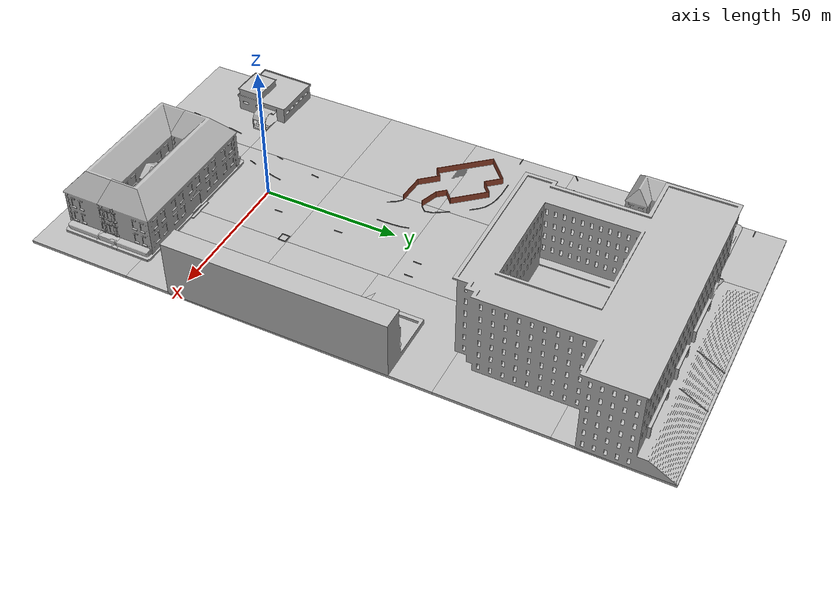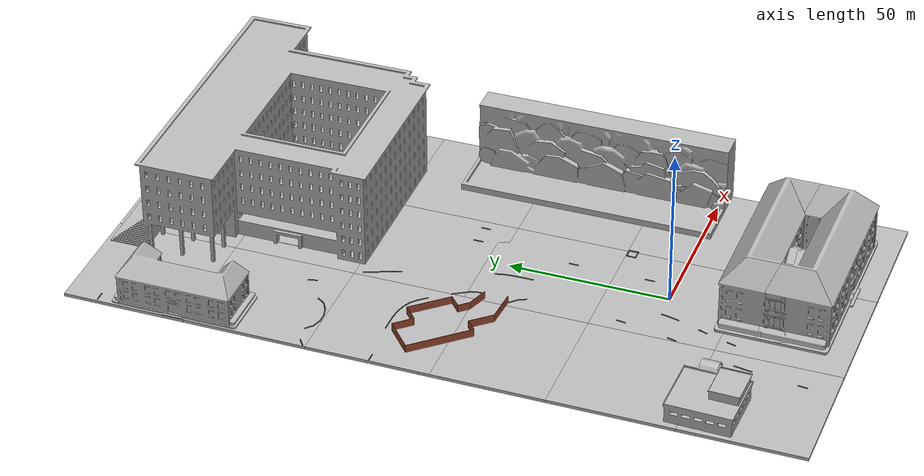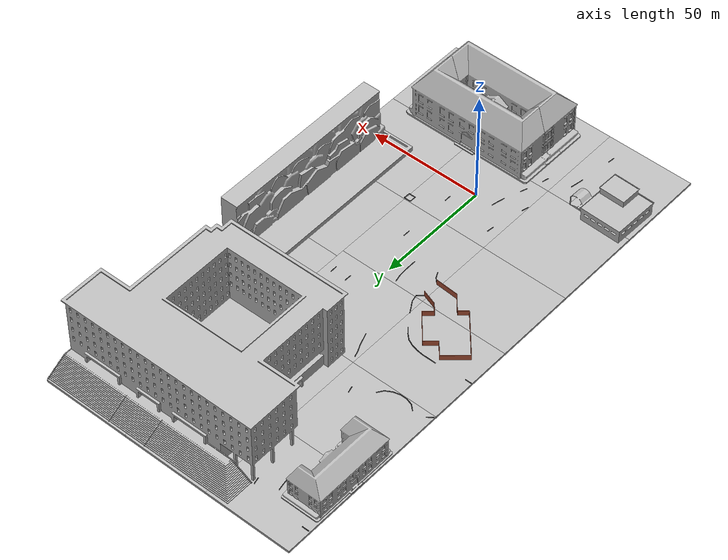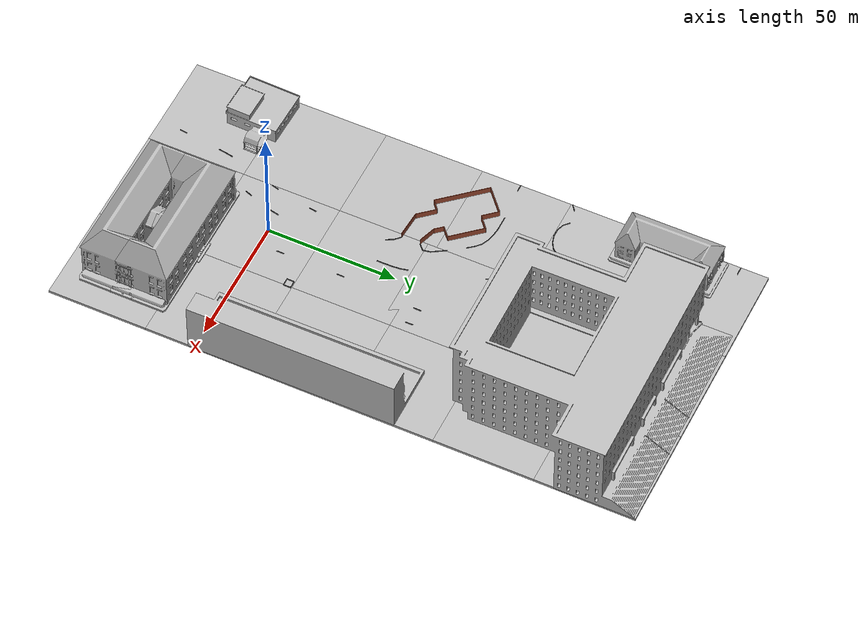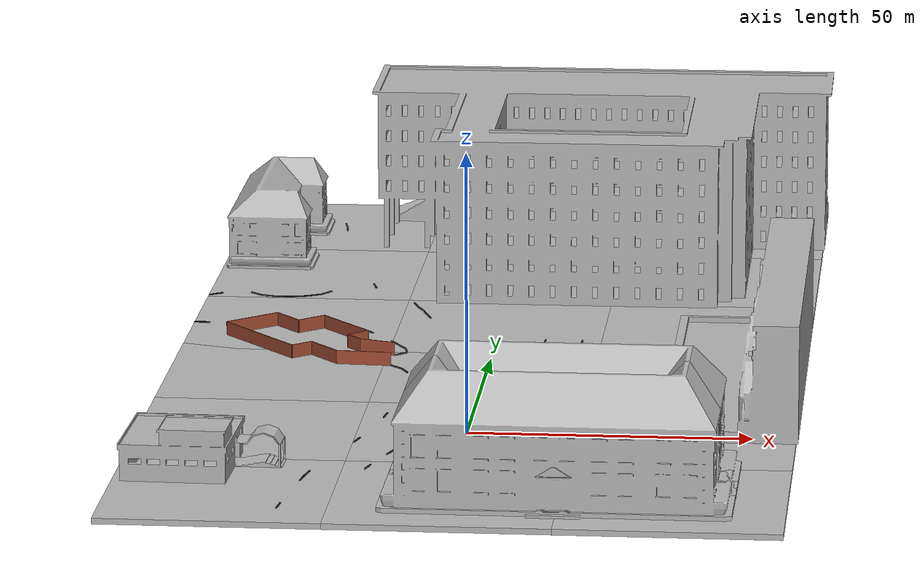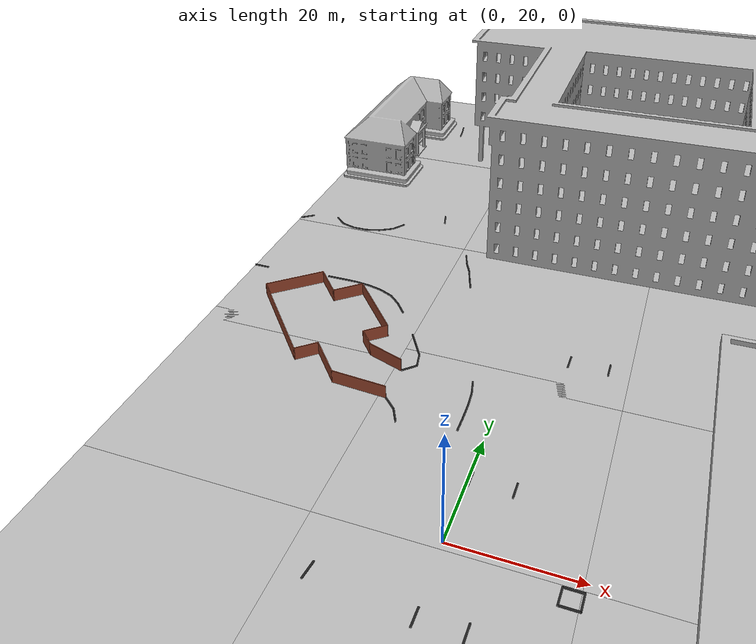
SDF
<sdf version="1.7">
 <world name="default">
  <light name="sun" type="directional">
   <pose>0 0 10 0 -0 0</pose>
   <diffuse>0.8 0.8 0.8 1</diffuse>
   <specular>0.2 0.2 0.2 1</specular>
   <attenuation>
    <range>1000</range>
    <constant>0.9</constant>
    <linear>0.01</linear>
    <quadratic>0.001</quadratic>
   </attenuation>
   <direction>-0.5 0.1 -0.9</direction>
   <spot><inner_angle>0</inner_angle><outer_angle>0</outer_angle><falloff>0</falloff></spot>
  </light>
  <plugin name="map" filename="libStaticMapPlugin.so">
   <center>36.6499 127.4969</center>
   <world_size>100</world_size>
   <map_type>satellite</map_type>
   <api_key>AIzaSyAgAc9EM1IBPvdNT30DDfyu5QpUF6_QtZM</api_key>
   <use_cache>0</use_cache>
  </plugin>
  <gravity>0 0 -9.8</gravity>
  <magnetic_field>6e-06 2.3e-05 -4.2e-05</magnetic_field>
  <atmosphere type="adiabatic"/>
  <physics type="ode">
   <max_step_size>0.001</max_step_size>
   <real_time_factor>1</real_time_factor>
   <real_time_update_rate>1000</real_time_update_rate>
  </physics>
  <scene><ambient>0.4 0.4 0.4 1</ambient><background>0.7 0.7 0.7 1</background><shadows>1</shadows></scene>
  <spherical_coordinates>
   <surface_model>EARTH_WGS84</surface_model>
   <latitude_deg>0</latitude_deg>
   <longitude_deg>0</longitude_deg>
   <elevation>0</elevation>
   <heading_deg>0</heading_deg>
  </spherical_coordinates>
  <model name="parking_5">
   <pose>-25.9065 69.2029 0 0 0 -0.06442</pose>
   <link name="Wall_116">
    <collision name="Wall_116_Collision">
     <geometry><box><size>11.5 0.15 2.5</size></box></geometry>
     <pose>0 0 1.25 0 -0 0</pose>
    </collision>
    <visual name="Wall_116_Visual">
     <pose>0 0 1.25 0 -0 0</pose>
     <geometry><box><size>11.5 0.15 2.5</size></box></geometry>
     <material>
      <script><uri>file://media/materials/scripts/gazebo.material</uri><name>Gazebo/Bricks</name></script>
      <ambient>1 1 1 1</ambient>
     </material>
     <meta><layer>0</layer></meta>
    </visual>
    <pose>-19.8928 -2.91219 0 0 -0 -2.35619</pose>
   </link>
   <link name="Wall_117">
    <collision name="Wall_117_Collision">
     <geometry><box><size>21.25 0.15 2.5</size></box></geometry>
     <pose>0 0 1.25 0 -0 0</pose>
    </collision>
    <visual name="Wall_117_Visual">
     <pose>0 0 1.25 0 -0 0</pose>
     <geometry><box><size>21.25 0.15 2.5</size></box></geometry>
     <material>
      <script><uri>file://media/materials/scripts/gazebo.material</uri><name>Gazebo/Bricks</name></script>
      <ambient>1 1 1 1</ambient>
     </material>
     <meta><layer>0</layer></meta>
    </visual>
    <pose>-16.4456 -14.385 0 0 -0 -0.785398</pose>
   </link>
   <link name="Wall_118">
    <collision name="Wall_118_Collision">
     <geometry><box><size>4.5 0.15 2.5</size></box></geometry>
     <pose>0 0 1.25 0 -0 0</pose>
    </collision>
    <visual name="Wall_118_Visual">
     <pose>0 0 1.25 0 -0 0</pose>
     <geometry><box><size>4.5 0.15 2.5</size></box></geometry>
     <material>
      <script><uri>file://media/materials/scripts/gazebo.material</uri><name>Gazebo/Bricks</name></script>
      <ambient>1 1 1 1</ambient>
     </material>
     <meta><layer>0</layer></meta>
    </visual>
    <pose>-7.44772 -20.307 0 0 -0 0.785398</pose>
   </link>
   <link name="Wall_119">
    <collision name="Wall_119_Collision">
     <geometry><box><size>8.25 0.15 2.5</size></box></geometry>
     <pose>0 0 1.25 0 -0 0</pose>
    </collision>
    <visual name="Wall_119_Visual">
     <pose>0 0 1.25 0 -0 0</pose>
     <geometry><box><size>8.25 0.15 2.5</size></box></geometry>
     <material>
      <script><uri>file://media/materials/scripts/gazebo.material</uri><name>Gazebo/Bricks</name></script>
      <ambient>1 1 1 1</ambient>
     </material>
     <meta><layer>0</layer></meta>
    </visual>
    <pose>-3.04598 -21.6328 0 0 -0 -0.785398</pose>
   </link>
   <link name="Wall_120">
    <collision name="Wall_120_Collision">
     <geometry><box><size>10 0.15 2.5</size></box></geometry>
     <pose>0 0 1.25 0 -0 0</pose>
    </collision>
    <visual name="Wall_120_Visual">
     <pose>0 0 1.25 0 -0 0</pose>
     <geometry><box><size>10 0.15 2.5</size></box></geometry>
     <material>
      <script><uri>file://media/materials/scripts/gazebo.material</uri><name>Gazebo/Bricks</name></script>
      <ambient>1 1 1 1</ambient>
     </material>
     <meta><layer>0</layer></meta>
    </visual>
    <pose>4.7428 -24.4966 0 0 -0 0</pose>
   </link>
   <link name="Wall_122">
    <collision name="Wall_122_Collision">
     <geometry><box><size>7 0.15 2.5</size></box></geometry>
     <pose>0 0 1.25 0 -0 0</pose>
    </collision>
    <visual name="Wall_122_Visual">
     <pose>0 0 1.25 0 -0 0</pose>
     <geometry><box><size>7 0.15 2.5</size></box></geometry>
     <material>
      <script><uri>file://media/materials/scripts/gazebo.material</uri><name>Gazebo/Bricks</name></script>
      <ambient>1 1 1 1</ambient>
     </material>
     <meta><layer>0</layer></meta>
    </visual>
    <pose>-13.4581 -1.3212 0 0 -0 -0.785398</pose>
   </link>
   <link name="Wall_123">
    <collision name="Wall_123_Collision">
     <geometry><box><size>6 0.15 2.5</size></box></geometry>
     <pose>0 0 1.25 0 -0 0</pose>
    </collision>
    <visual name="Wall_123_Visual">
     <pose>0 0 1.25 0 -0 0</pose>
     <geometry><box><size>6 0.15 2.5</size></box></geometry>
     <material>
      <script><uri>file://media/materials/scripts/gazebo.material</uri><name>Gazebo/Bricks</name></script>
      <ambient>1 1 1 1</ambient>
     </material>
     <meta><layer>0</layer></meta>
    </visual>
    <pose>-8.968 -1.67475 0 0 -0 0.785398</pose>
   </link>
   <link name="Wall_124">
    <collision name="Wall_124_Collision">
     <geometry><box><size>14.25 0.15 2.5</size></box></geometry>
     <pose>0 0 1.25 0 -0 0</pose>
    </collision>
    <visual name="Wall_124_Visual">
     <pose>0 0 1.25 0 -0 0</pose>
     <geometry><box><size>14.25 0.15 2.5</size></box></geometry>
     <material>
      <script><uri>file://media/materials/scripts/gazebo.material</uri><name>Gazebo/Bricks</name></script>
      <ambient>1 1 1 1</ambient>
     </material>
     <meta><layer>0</layer></meta>
    </visual>
    <pose>-1.91461 -4.59157 0 0 -0 -0.785398</pose>
   </link>
   <link name="Wall_125">
    <collision name="Wall_125_Collision">
     <geometry><box><size>4.75 0.15 2.5</size></box></geometry>
     <pose>0 0 1.25 0 -0 0</pose>
    </collision>
    <visual name="Wall_125_Visual">
     <pose>0 0 1.25 0 -0 0</pose>
     <geometry><box><size>4.75 0.15 2.5</size></box></geometry>
     <material>
      <script><uri>file://media/materials/scripts/gazebo.material</uri><name>Gazebo/Bricks</name></script>
      <ambient>1 1 1 1</ambient>
     </material>
     <meta><layer>0</layer></meta>
    </visual>
    <pose>1.44415 -11.203 0 0 -0 -2.35619</pose>
   </link>
   <link name="Wall_131">
    <collision name="Wall_131_Collision">
     <geometry><box><size>4 0.15 2.5</size></box></geometry>
     <pose>0 0 1.25 0 -0 0</pose>
    </collision>
    <visual name="Wall_131_Visual">
     <pose>0 0 1.25 0 -0 0</pose>
     <geometry><box><size>4 0.15 2.5</size></box></geometry>
     <material>
      <script><uri>file://media/materials/scripts/gazebo.material</uri><name>Gazebo/Bricks</name></script>
      <ambient>1 1 1 1</ambient>
     </material>
     <meta><layer>0</layer></meta>
    </visual>
    <pose>1.17899 -14.1905 0 0 -0 -0.785398</pose>
   </link>
   <link name="Wall_132">
    <collision name="Wall_132_Collision">
     <geometry><box><size>7 0.15 2.5</size></box></geometry>
     <pose>0 0 1.25 0 -0 0</pose>
    </collision>
    <visual name="Wall_132_Visual">
     <pose>0 0 1.25 0 -0 0</pose>
     <geometry><box><size>7 0.15 2.5</size></box></geometry>
     <material>
      <script><uri>file://media/materials/scripts/gazebo.material</uri><name>Gazebo/Bricks</name></script>
      <ambient>1 1 1 1</ambient>
     </material>
     <meta><layer>0</layer></meta>
    </visual>
    <pose>5.84846 -16.4382 0 0 -0 -0.261799</pose>
   </link>
   <static>1</static>
  </model>
  <model name="bar2">
   <static>1</static>
   <link name="link_3">
    <inertial>
     <mass>1</mass>
     <inertia>
      <ixx>0.166667</ixx>
      <ixy>0</ixy>
      <ixz>0</ixz>
      <iyy>0.166667</iyy>
      <iyz>0</iyz>
      <izz>0.166667</izz>
     </inertia>
    </inertial>
    <pose>4.47991 -0.091961 0 0 -0 0</pose>
    <visual name="visual">
     <geometry>
      <mesh><uri>/home/leejeonghun/model_editor_models/bar2.dae</uri><scale>1 1 1</scale></mesh>
     </geometry>
     <material>
      <lighting>1</lighting>
      <script><uri>file://media/materials/scripts/gazebo.material</uri><name>Gazebo/Black</name></script>
      <shader type="pixel"/>
     </material>
    </visual>
    <collision name="collision">
     <geometry>
      <mesh><uri>/home/leejeonghun/model_editor_models/bar2.dae</uri><scale>1 1 1</scale></mesh>
     </geometry>
     <surface>
      <friction>
       <ode><mu>1</mu><mu2>1</mu2><fdir1>0 0 0</fdir1><slip1>0</slip1><slip2>0</slip2></ode>
       <torsional>
        <coefficient>1</coefficient>
        <patch_radius>0</patch_radius>
        <surface_radius>0</surface_radius>
        <use_patch_radius>1</use_patch_radius>
        <ode><slip>0</slip></ode>
       </torsional>
      </friction>
      <bounce><restitution_coefficient>0</restitution_coefficient><threshold>1e+06</threshold></bounce>
      <contact>
       <collide_without_contact>0</collide_without_contact>
       <collide_without_contact_bitmask>1</collide_without_contact_bitmask>
       <collide_bitmask>1</collide_bitmask>
       <ode>
        <soft_cfm>0</soft_cfm>
        <soft_erp>0.2</soft_erp>
        <kp>1e+13</kp>
        <kd>1</kd>
        <max_vel>0.01</max_vel>
        <min_depth>0</min_depth>
       </ode>
       <bullet>
        <split_impulse>1</split_impulse>
        <split_impulse_penetration_threshold>-0.01</split_impulse_penetration_threshold>
        <soft_cfm>0</soft_cfm>
        <soft_erp>0.2</soft_erp>
        <kp>1e+13</kp>
        <kd>1</kd>
       </bullet>
      </contact>
     </surface>
    </collision>
   </link>
   <static>0</static>
   <pose>-9.21362 27.7112 0 0 0 -0.764072</pose>
  </model>
  <model name="bar2_0">
   <static>1</static>
   <link name="link_3">
    <inertial>
     <mass>1</mass>
     <inertia>
      <ixx>0.166667</ixx>
      <ixy>0</ixy>
      <ixz>0</ixz>
      <iyy>0.166667</iyy>
      <iyz>0</iyz>
      <izz>0.166667</izz>
     </inertia>
    </inertial>
    <pose>4.47991 -0.091961 0 0 -0 0</pose>
    <visual name="visual">
     <geometry>
      <mesh><uri>/home/leejeonghun/model_editor_models/bar2.dae</uri><scale>1 1 1</scale></mesh>
     </geometry>
     <material>
      <lighting>1</lighting>
      <script><uri>file://media/materials/scripts/gazebo.material</uri><name>Gazebo/Black</name></script>
      <shader type="pixel"/>
     </material>
    </visual>
    <collision name="collision">
     <geometry>
      <mesh><uri>/home/leejeonghun/model_editor_models/bar2.dae</uri><scale>1 1 1</scale></mesh>
     </geometry>
     <surface>
      <friction>
       <ode><mu>1</mu><mu2>1</mu2><fdir1>0 0 0</fdir1><slip1>0</slip1><slip2>0</slip2></ode>
       <torsional>
        <coefficient>1</coefficient>
        <patch_radius>0</patch_radius>
        <surface_radius>0</surface_radius>
        <use_patch_radius>1</use_patch_radius>
        <ode><slip>0</slip></ode>
       </torsional>
      </friction>
      <bounce><restitution_coefficient>0</restitution_coefficient><threshold>1e+06</threshold></bounce>
      <contact>
       <collide_without_contact>0</collide_without_contact>
       <collide_without_contact_bitmask>1</collide_without_contact_bitmask>
       <collide_bitmask>1</collide_bitmask>
       <ode>
        <soft_cfm>0</soft_cfm>
        <soft_erp>0.2</soft_erp>
        <kp>1e+13</kp>
        <kd>1</kd>
        <max_vel>0.01</max_vel>
        <min_depth>0</min_depth>
       </ode>
       <bullet>
        <split_impulse>1</split_impulse>
        <split_impulse_penetration_threshold>-0.01</split_impulse_penetration_threshold>
        <soft_cfm>0</soft_cfm>
        <soft_erp>0.2</soft_erp>
        <kp>1e+13</kp>
        <kd>1</kd>
       </bullet>
      </contact>
     </surface>
    </collision>
   </link>
   <static>0</static>
   <pose>-12.9063 23.7829 0 0 0 -1.0978</pose>
  </model>
  <model name="bar2_1">
   <static>1</static>
   <link name="link_3">
    <inertial>
     <mass>1</mass>
     <inertia>
      <ixx>0.166667</ixx>
      <ixy>0</ixy>
      <ixz>0</ixz>
      <iyy>0.166667</iyy>
      <iyz>0</iyz>
      <izz>0.166667</izz>
     </inertia>
    </inertial>
    <pose>4.47991 -0.091961 0 0 -0 0</pose>
    <visual name="visual">
     <geometry>
      <mesh><uri>/home/leejeonghun/model_editor_models/bar2.dae</uri><scale>1 1 1</scale></mesh>
     </geometry>
     <material>
      <lighting>1</lighting>
      <script><uri>file://media/materials/scripts/gazebo.material</uri><name>Gazebo/Black</name></script>
      <shader type="pixel"/>
     </material>
    </visual>
    <collision name="collision">
     <geometry>
      <mesh><uri>/home/leejeonghun/model_editor_models/bar2.dae</uri><scale>1 1 1</scale></mesh>
     </geometry>
     <surface>
      <friction>
       <ode><mu>1</mu><mu2>1</mu2><fdir1>0 0 0</fdir1><slip1>0</slip1><slip2>0</slip2></ode>
       <torsional>
        <coefficient>1</coefficient>
        <patch_radius>0</patch_radius>
        <surface_radius>0</surface_radius>
        <use_patch_radius>1</use_patch_radius>
        <ode><slip>0</slip></ode>
       </torsional>
      </friction>
      <bounce><restitution_coefficient>0</restitution_coefficient><threshold>1e+06</threshold></bounce>
      <contact>
       <collide_without_contact>0</collide_without_contact>
       <collide_without_contact_bitmask>1</collide_without_contact_bitmask>
       <collide_bitmask>1</collide_bitmask>
       <ode>
        <soft_cfm>0</soft_cfm>
        <soft_erp>0.2</soft_erp>
        <kp>1e+13</kp>
        <kd>1</kd>
        <max_vel>0.01</max_vel>
        <min_depth>0</min_depth>
       </ode>
       <bullet>
        <split_impulse>1</split_impulse>
        <split_impulse_penetration_threshold>-0.01</split_impulse_penetration_threshold>
        <soft_cfm>0</soft_cfm>
        <soft_erp>0.2</soft_erp>
        <kp>1e+13</kp>
        <kd>1</kd>
       </bullet>
      </contact>
     </surface>
    </collision>
   </link>
   <static>0</static>
   <pose>-7.36679 25.1562 0 0 -0 1.44352</pose>
  </model>
  <model name="bar2_2">
   <static>1</static>
   <link name="link_3">
    <inertial>
     <mass>1</mass>
     <inertia>
      <ixx>0.166667</ixx>
      <ixy>0</ixy>
      <ixz>0</ixz>
      <iyy>0.166667</iyy>
      <iyz>0</iyz>
      <izz>0.166667</izz>
     </inertia>
    </inertial>
    <pose>4.47991 -0.091961 0 0 -0 0</pose>
    <visual name="visual">
     <geometry>
      <mesh><uri>/home/leejeonghun/model_editor_models/bar2.dae</uri><scale>1 1 1</scale></mesh>
     </geometry>
     <material>
      <lighting>1</lighting>
      <script><uri>file://media/materials/scripts/gazebo.material</uri><name>Gazebo/Black</name></script>
      <shader type="pixel"/>
     </material>
    </visual>
    <collision name="collision">
     <geometry>
      <mesh><uri>/home/leejeonghun/model_editor_models/bar2.dae</uri><scale>1 1 1</scale></mesh>
     </geometry>
     <surface>
      <friction>
       <ode><mu>1</mu><mu2>1</mu2><fdir1>0 0 0</fdir1><slip1>0</slip1><slip2>0</slip2></ode>
       <torsional>
        <coefficient>1</coefficient>
        <patch_radius>0</patch_radius>
        <surface_radius>0</surface_radius>
        <use_patch_radius>1</use_patch_radius>
        <ode><slip>0</slip></ode>
       </torsional>
      </friction>
      <bounce><restitution_coefficient>0</restitution_coefficient><threshold>1e+06</threshold></bounce>
      <contact>
       <collide_without_contact>0</collide_without_contact>
       <collide_without_contact_bitmask>1</collide_without_contact_bitmask>
       <collide_bitmask>1</collide_bitmask>
       <ode>
        <soft_cfm>0</soft_cfm>
        <soft_erp>0.2</soft_erp>
        <kp>1e+13</kp>
        <kd>1</kd>
        <max_vel>0.01</max_vel>
        <min_depth>0</min_depth>
       </ode>
       <bullet>
        <split_impulse>1</split_impulse>
        <split_impulse_penetration_threshold>-0.01</split_impulse_penetration_threshold>
        <soft_cfm>0</soft_cfm>
        <soft_erp>0.2</soft_erp>
        <kp>1e+13</kp>
        <kd>1</kd>
       </bullet>
      </contact>
     </surface>
    </collision>
   </link>
   <static>0</static>
   <pose>-8.85128 7.56304 0 0 -0 1.31671</pose>
  </model>
  <model name="bar2_3">
   <static>1</static>
   <link name="link_3">
    <inertial>
     <mass>1</mass>
     <inertia>
      <ixx>0.166667</ixx>
      <ixy>0</ixy>
      <ixz>0</ixz>
      <iyy>0.166667</iyy>
      <iyz>0</iyz>
      <izz>0.166667</izz>
     </inertia>
    </inertial>
    <pose>4.47991 -0.091961 0 0 -0 0</pose>
    <visual name="visual">
     <geometry>
      <mesh><uri>/home/leejeonghun/model_editor_models/bar2.dae</uri><scale>1 1 1</scale></mesh>
     </geometry>
     <material>
      <lighting>1</lighting>
      <script><uri>file://media/materials/scripts/gazebo.material</uri><name>Gazebo/Black</name></script>
      <shader type="pixel"/>
     </material>
    </visual>
    <collision name="collision">
     <geometry>
      <mesh><uri>/home/leejeonghun/model_editor_models/bar2.dae</uri><scale>1 1 1</scale></mesh>
     </geometry>
     <surface>
      <friction>
       <ode><mu>1</mu><mu2>1</mu2><fdir1>0 0 0</fdir1><slip1>0</slip1><slip2>0</slip2></ode>
       <torsional>
        <coefficient>1</coefficient>
        <patch_radius>0</patch_radius>
        <surface_radius>0</surface_radius>
        <use_patch_radius>1</use_patch_radius>
        <ode><slip>0</slip></ode>
       </torsional>
      </friction>
      <bounce><restitution_coefficient>0</restitution_coefficient><threshold>1e+06</threshold></bounce>
      <contact>
       <collide_without_contact>0</collide_without_contact>
       <collide_without_contact_bitmask>1</collide_without_contact_bitmask>
       <collide_bitmask>1</collide_bitmask>
       <ode>
        <soft_cfm>0</soft_cfm>
        <soft_erp>0.2</soft_erp>
        <kp>1e+13</kp>
        <kd>1</kd>
        <max_vel>0.01</max_vel>
        <min_depth>0</min_depth>
       </ode>
       <bullet>
        <split_impulse>1</split_impulse>
        <split_impulse_penetration_threshold>-0.01</split_impulse_penetration_threshold>
        <soft_cfm>0</soft_cfm>
        <soft_erp>0.2</soft_erp>
        <kp>1e+13</kp>
        <kd>1</kd>
       </bullet>
      </contact>
     </surface>
    </collision>
   </link>
   <static>0</static>
   <pose>-15.9336 -13.5824 0 0 -0 1.37702</pose>
  </model>
  <model name="bar2_4">
   <static>1</static>
   <link name="link_3">
    <inertial>
     <mass>1</mass>
     <inertia>
      <ixx>0.166667</ixx>
      <ixy>0</ixy>
      <ixz>0</ixz>
      <iyy>0.166667</iyy>
      <iyz>0</iyz>
      <izz>0.166667</izz>
     </inertia>
    </inertial>
    <pose>4.47991 -0.091961 0 0 -0 0</pose>
    <visual name="visual">
     <geometry>
      <mesh><uri>/home/leejeonghun/model_editor_models/bar2.dae</uri><scale>1 1 1</scale></mesh>
     </geometry>
     <material>
      <lighting>1</lighting>
      <script><uri>file://media/materials/scripts/gazebo.material</uri><name>Gazebo/Black</name></script>
      <shader type="pixel"/>
     </material>
    </visual>
    <collision name="collision">
     <geometry>
      <mesh><uri>/home/leejeonghun/model_editor_models/bar2.dae</uri><scale>1 1 1</scale></mesh>
     </geometry>
     <surface>
      <friction>
       <ode><mu>1</mu><mu2>1</mu2><fdir1>0 0 0</fdir1><slip1>0</slip1><slip2>0</slip2></ode>
       <torsional>
        <coefficient>1</coefficient>
        <patch_radius>0</patch_radius>
        <surface_radius>0</surface_radius>
        <use_patch_radius>1</use_patch_radius>
        <ode><slip>0</slip></ode>
       </torsional>
      </friction>
      <bounce><restitution_coefficient>0</restitution_coefficient><threshold>1e+06</threshold></bounce>
      <contact>
       <collide_without_contact>0</collide_without_contact>
       <collide_without_contact_bitmask>1</collide_without_contact_bitmask>
       <collide_bitmask>1</collide_bitmask>
       <ode>
        <soft_cfm>0</soft_cfm>
        <soft_erp>0.2</soft_erp>
        <kp>1e+13</kp>
        <kd>1</kd>
        <max_vel>0.01</max_vel>
        <min_depth>0</min_depth>
       </ode>
       <bullet>
        <split_impulse>1</split_impulse>
        <split_impulse_penetration_threshold>-0.01</split_impulse_penetration_threshold>
        <soft_cfm>0</soft_cfm>
        <soft_erp>0.2</soft_erp>
        <kp>1e+13</kp>
        <kd>1</kd>
       </bullet>
      </contact>
     </surface>
    </collision>
   </link>
   <static>0</static>
   <pose>-17.1899 -16.0509 0 0 -0 1.42906</pose>
  </model>
  <model name="map_satellite_36.6499_127.4969_100_100">
   <static>1</static>
   <link name="link">
    <collision name="collision">
     <pose>0 0 -0.5 0 -0 0</pose>
     <geometry><box><size>114.985 114.985 1</size></box></geometry>
    </collision>
    <visual name="visual0_0">
     <pose>-38.3283 38.3283 -0.5 0 -0 1.5708</pose>
     <geometry><box><size>38.3283 38.3283 1</size></box></geometry>
     <material>
      <script>
       <uri>model://map_satellite_36.6499_127.4969_100_100/materials/scripts</uri>
       <uri>model://map_satellite_36.6499_127.4969_100_100/materials/textures</uri>
       <name>map_satellite_36.6499_127.4969_100_100/0_0</name>
      </script>
     </material>
    </visual>
    <visual name="visual0_1">
     <pose>0 38.3283 -0.5 0 -0 1.5708</pose>
     <geometry><box><size>38.3283 38.3283 1</size></box></geometry>
     <material>
      <script>
       <uri>model://map_satellite_36.6499_127.4969_100_100/materials/scripts</uri>
       <uri>model://map_satellite_36.6499_127.4969_100_100/materials/textures</uri>
       <name>map_satellite_36.6499_127.4969_100_100/0_1</name>
      </script>
     </material>
    </visual>
    <visual name="visual0_2">
     <pose>38.3283 38.3283 -0.5 0 -0 1.5708</pose>
     <geometry><box><size>38.3283 38.3283 1</size></box></geometry>
     <material>
      <script>
       <uri>model://map_satellite_36.6499_127.4969_100_100/materials/scripts</uri>
       <uri>model://map_satellite_36.6499_127.4969_100_100/materials/textures</uri>
       <name>map_satellite_36.6499_127.4969_100_100/0_2</name>
      </script>
     </material>
    </visual>
    <visual name="visual1_0">
     <pose>-38.3283 0 -0.5 0 -0 1.5708</pose>
     <geometry><box><size>38.3283 38.3283 1</size></box></geometry>
     <material>
      <script>
       <uri>model://map_satellite_36.6499_127.4969_100_100/materials/scripts</uri>
       <uri>model://map_satellite_36.6499_127.4969_100_100/materials/textures</uri>
       <name>map_satellite_36.6499_127.4969_100_100/1_0</name>
      </script>
     </material>
    </visual>
    <visual name="visual1_1">
     <pose>0 0 -0.5 0 -0 1.5708</pose>
     <geometry><box><size>38.3283 38.3283 1</size></box></geometry>
     <material>
      <script>
       <uri>model://map_satellite_36.6499_127.4969_100_100/materials/scripts</uri>
       <uri>model://map_satellite_36.6499_127.4969_100_100/materials/textures</uri>
       <name>map_satellite_36.6499_127.4969_100_100/1_1</name>
      </script>
     </material>
    </visual>
    <visual name="visual1_2">
     <pose>38.3283 0 -0.5 0 -0 1.5708</pose>
     <geometry><box><size>38.3283 38.3283 1</size></box></geometry>
     <material>
      <script>
       <uri>model://map_satellite_36.6499_127.4969_100_100/materials/scripts</uri>
       <uri>model://map_satellite_36.6499_127.4969_100_100/materials/textures</uri>
       <name>map_satellite_36.6499_127.4969_100_100/1_2</name>
      </script>
     </material>
    </visual>
    <visual name="visual2_0">
     <pose>-38.3283 -38.3283 -0.5 0 -0 1.5708</pose>
     <geometry><box><size>38.3283 38.3283 1</size></box></geometry>
     <material>
      <script>
       <uri>model://map_satellite_36.6499_127.4969_100_100/materials/scripts</uri>
       <uri>model://map_satellite_36.6499_127.4969_100_100/materials/textures</uri>
       <name>map_satellite_36.6499_127.4969_100_100/2_0</name>
      </script>
     </material>
    </visual>
    <visual name="visual2_1">
     <pose>0 -38.3283 -0.5 0 -0 1.5708</pose>
     <geometry><box><size>38.3283 38.3283 1</size></box></geometry>
     <material>
      <script>
       <uri>model://map_satellite_36.6499_127.4969_100_100/materials/scripts</uri>
       <uri>model://map_satellite_36.6499_127.4969_100_100/materials/textures</uri>
       <name>map_satellite_36.6499_127.4969_100_100/2_1</name>
      </script>
     </material>
    </visual>
    <visual name="visual2_2">
     <pose>38.3283 -38.3283 -0.5 0 -0 1.5708</pose>
     <geometry><box><size>38.3283 38.3283 1</size></box></geometry>
     <material>
      <script>
       <uri>model://map_satellite_36.6499_127.4969_100_100/materials/scripts</uri>
       <uri>model://map_satellite_36.6499_127.4969_100_100/materials/textures</uri>
       <name>map_satellite_36.6499_127.4969_100_100/2_2</name>
      </script>
     </material>
    </visual>
   </link>
   <pose>0.014059 -0.283883 0 0 -0 0</pose>
  </model>
  <model name="bar2_5">
   <static>1</static>
   <link name="link_3">
    <inertial>
     <mass>1</mass>
     <inertia>
      <ixx>0.166667</ixx>
      <ixy>0</ixy>
      <ixz>0</ixz>
      <iyy>0.166667</iyy>
      <iyz>0</iyz>
      <izz>0.166667</izz>
     </inertia>
    </inertial>
    <pose>4.47991 -0.091961 0 0 -0 0</pose>
    <visual name="visual">
     <geometry>
      <mesh><uri>/home/leejeonghun/model_editor_models/bar2.dae</uri><scale>1 1 1</scale></mesh>
     </geometry>
     <material>
      <lighting>1</lighting>
      <script><uri>file://media/materials/scripts/gazebo.material</uri><name>Gazebo/Black</name></script>
      <shader type="pixel"/>
     </material>
    </visual>
    <collision name="collision">
     <geometry>
      <mesh><uri>/home/leejeonghun/model_editor_models/bar2.dae</uri><scale>1 1 1</scale></mesh>
     </geometry>
     <surface>
      <friction>
       <ode><mu>1</mu><mu2>1</mu2><fdir1>0 0 0</fdir1><slip1>0</slip1><slip2>0</slip2></ode>
       <torsional>
        <coefficient>1</coefficient>
        <patch_radius>0</patch_radius>
        <surface_radius>0</surface_radius>
        <use_patch_radius>1</use_patch_radius>
        <ode><slip>0</slip></ode>
       </torsional>
      </friction>
      <bounce><restitution_coefficient>0</restitution_coefficient><threshold>1e+06</threshold></bounce>
      <contact>
       <collide_without_contact>0</collide_without_contact>
       <collide_without_contact_bitmask>1</collide_without_contact_bitmask>
       <collide_bitmask>1</collide_bitmask>
       <ode>
        <soft_cfm>0</soft_cfm>
        <soft_erp>0.2</soft_erp>
        <kp>1e+13</kp>
        <kd>1</kd>
        <max_vel>0.01</max_vel>
        <min_depth>0</min_depth>
       </ode>
       <bullet>
        <split_impulse>1</split_impulse>
        <split_impulse_penetration_threshold>-0.01</split_impulse_penetration_threshold>
        <soft_cfm>0</soft_cfm>
        <soft_erp>0.2</soft_erp>
        <kp>1e+13</kp>
        <kd>1</kd>
       </bullet>
      </contact>
     </surface>
    </collision>
   </link>
   <static>0</static>
   <pose>-19.7754 -32.5932 0 0 -0 1.46324</pose>
  </model>
  <model name="bar2_6">
   <static>1</static>
   <link name="link_3">
    <inertial>
     <mass>1</mass>
     <inertia>
      <ixx>0.166667</ixx>
      <ixy>0</ixy>
      <ixz>0</ixz>
      <iyy>0.166667</iyy>
      <iyz>0</iyz>
      <izz>0.166667</izz>
     </inertia>
    </inertial>
    <pose>4.47991 -0.091961 0 0 -0 0</pose>
    <visual name="visual">
     <geometry>
      <mesh><uri>/home/leejeonghun/model_editor_models/bar2.dae</uri><scale>1 1 1</scale></mesh>
     </geometry>
     <material>
      <lighting>1</lighting>
      <script><uri>file://media/materials/scripts/gazebo.material</uri><name>Gazebo/Black</name></script>
      <shader type="pixel"/>
     </material>
    </visual>
    <collision name="collision">
     <geometry>
      <mesh><uri>/home/leejeonghun/model_editor_models/bar2.dae</uri><scale>1 1 1</scale></mesh>
     </geometry>
     <surface>
      <friction>
       <ode><mu>1</mu><mu2>1</mu2><fdir1>0 0 0</fdir1><slip1>0</slip1><slip2>0</slip2></ode>
       <torsional>
        <coefficient>1</coefficient>
        <patch_radius>0</patch_radius>
        <surface_radius>0</surface_radius>
        <use_patch_radius>1</use_patch_radius>
        <ode><slip>0</slip></ode>
       </torsional>
      </friction>
      <bounce><restitution_coefficient>0</restitution_coefficient><threshold>1e+06</threshold></bounce>
      <contact>
       <collide_without_contact>0</collide_without_contact>
       <collide_without_contact_bitmask>1</collide_without_contact_bitmask>
       <collide_bitmask>1</collide_bitmask>
       <ode>
        <soft_cfm>0</soft_cfm>
        <soft_erp>0.2</soft_erp>
        <kp>1e+13</kp>
        <kd>1</kd>
        <max_vel>0.01</max_vel>
        <min_depth>0</min_depth>
       </ode>
       <bullet>
        <split_impulse>1</split_impulse>
        <split_impulse_penetration_threshold>-0.01</split_impulse_penetration_threshold>
        <soft_cfm>0</soft_cfm>
        <soft_erp>0.2</soft_erp>
        <kp>1e+13</kp>
        <kd>1</kd>
       </bullet>
      </contact>
     </surface>
    </collision>
   </link>
   <static>0</static>
   <pose>-1.09413 59.2112 0 0 -0 0.766971</pose>
  </model>
  <model name="bar2_7">
   <static>1</static>
   <link name="link_3">
    <inertial>
     <mass>1</mass>
     <inertia>
      <ixx>0.166667</ixx>
      <ixy>0</ixy>
      <ixz>0</ixz>
      <iyy>0.166667</iyy>
      <iyz>0</iyz>
      <izz>0.166667</izz>
     </inertia>
    </inertial>
    <pose>4.47991 -0.091961 0 0 -0 0</pose>
    <visual name="visual">
     <geometry>
      <mesh><uri>/home/leejeonghun/model_editor_models/bar2.dae</uri><scale>1 1 1</scale></mesh>
     </geometry>
     <material>
      <lighting>1</lighting>
      <script><uri>file://media/materials/scripts/gazebo.material</uri><name>Gazebo/Black</name></script>
      <shader type="pixel"/>
     </material>
    </visual>
    <collision name="collision">
     <geometry>
      <mesh><uri>/home/leejeonghun/model_editor_models/bar2.dae</uri><scale>1 1 1</scale></mesh>
     </geometry>
     <surface>
      <friction>
       <ode><mu>1</mu><mu2>1</mu2><fdir1>0 0 0</fdir1><slip1>0</slip1><slip2>0</slip2></ode>
       <torsional>
        <coefficient>1</coefficient>
        <patch_radius>0</patch_radius>
        <surface_radius>0</surface_radius>
        <use_patch_radius>1</use_patch_radius>
        <ode><slip>0</slip></ode>
       </torsional>
      </friction>
      <bounce><restitution_coefficient>0</restitution_coefficient><threshold>1e+06</threshold></bounce>
      <contact>
       <collide_without_contact>0</collide_without_contact>
       <collide_without_contact_bitmask>1</collide_without_contact_bitmask>
       <collide_bitmask>1</collide_bitmask>
       <ode>
        <soft_cfm>0</soft_cfm>
        <soft_erp>0.2</soft_erp>
        <kp>1e+13</kp>
        <kd>1</kd>
        <max_vel>0.01</max_vel>
        <min_depth>0</min_depth>
       </ode>
       <bullet>
        <split_impulse>1</split_impulse>
        <split_impulse_penetration_threshold>-0.01</split_impulse_penetration_threshold>
        <soft_cfm>0</soft_cfm>
        <soft_erp>0.2</soft_erp>
        <kp>1e+13</kp>
        <kd>1</kd>
       </bullet>
      </contact>
     </surface>
    </collision>
   </link>
   <static>0</static>
   <pose>-18.4742 37.8996 0 0 0 -1.36438</pose>
  </model>
  <model name="map_satellite_36.6509_127.4969_100_100">
   <static>1</static>
   <link name="link">
    <collision name="collision">
     <pose>0 0 -0.5 0 -0 0</pose>
     <geometry><box><size>114.983 114.983 1</size></box></geometry>
    </collision>
    <visual name="visual0_0">
     <pose>-38.3278 38.3278 -0.5 0 -0 1.5708</pose>
     <geometry><box><size>38.3278 38.3278 1</size></box></geometry>
     <material>
      <script>
       <uri>model://map_satellite_36.6509_127.4969_100_100/materials/scripts</uri>
       <uri>model://map_satellite_36.6509_127.4969_100_100/materials/textures</uri>
       <name>map_satellite_36.6509_127.4969_100_100/0_0</name>
      </script>
     </material>
    </visual>
    <visual name="visual0_1">
     <pose>0 38.3278 -0.5 0 -0 1.5708</pose>
     <geometry><box><size>38.3278 38.3278 1</size></box></geometry>
     <material>
      <script>
       <uri>model://map_satellite_36.6509_127.4969_100_100/materials/scripts</uri>
       <uri>model://map_satellite_36.6509_127.4969_100_100/materials/textures</uri>
       <name>map_satellite_36.6509_127.4969_100_100/0_1</name>
      </script>
     </material>
    </visual>
    <visual name="visual0_2">
     <pose>38.3278 38.3278 -0.5 0 -0 1.5708</pose>
     <geometry><box><size>38.3278 38.3278 1</size></box></geometry>
     <material>
      <script>
       <uri>model://map_satellite_36.6509_127.4969_100_100/materials/scripts</uri>
       <uri>model://map_satellite_36.6509_127.4969_100_100/materials/textures</uri>
       <name>map_satellite_36.6509_127.4969_100_100/0_2</name>
      </script>
     </material>
    </visual>
    <visual name="visual1_0">
     <pose>-38.3278 0 -0.5 0 -0 1.5708</pose>
     <geometry><box><size>38.3278 38.3278 1</size></box></geometry>
     <material>
      <script>
       <uri>model://map_satellite_36.6509_127.4969_100_100/materials/scripts</uri>
       <uri>model://map_satellite_36.6509_127.4969_100_100/materials/textures</uri>
       <name>map_satellite_36.6509_127.4969_100_100/1_0</name>
      </script>
     </material>
    </visual>
    <visual name="visual1_1">
     <pose>0 0 -0.5 0 -0 1.5708</pose>
     <geometry><box><size>38.3278 38.3278 1</size></box></geometry>
     <material>
      <script>
       <uri>model://map_satellite_36.6509_127.4969_100_100/materials/scripts</uri>
       <uri>model://map_satellite_36.6509_127.4969_100_100/materials/textures</uri>
       <name>map_satellite_36.6509_127.4969_100_100/1_1</name>
      </script>
     </material>
    </visual>
    <visual name="visual1_2">
     <pose>38.3278 0 -0.5 0 -0 1.5708</pose>
     <geometry><box><size>38.3278 38.3278 1</size></box></geometry>
     <material>
      <script>
       <uri>model://map_satellite_36.6509_127.4969_100_100/materials/scripts</uri>
       <uri>model://map_satellite_36.6509_127.4969_100_100/materials/textures</uri>
       <name>map_satellite_36.6509_127.4969_100_100/1_2</name>
      </script>
     </material>
    </visual>
    <visual name="visual2_0">
     <pose>-38.3278 -38.3278 -0.5 0 -0 1.5708</pose>
     <geometry><box><size>38.3278 38.3278 1</size></box></geometry>
     <material>
      <script>
       <uri>model://map_satellite_36.6509_127.4969_100_100/materials/scripts</uri>
       <uri>model://map_satellite_36.6509_127.4969_100_100/materials/textures</uri>
       <name>map_satellite_36.6509_127.4969_100_100/2_0</name>
      </script>
     </material>
    </visual>
    <visual name="visual2_1">
     <pose>0 -38.3278 -0.5 0 -0 1.5708</pose>
     <geometry><box><size>38.3278 38.3278 1</size></box></geometry>
     <material>
      <script>
       <uri>model://map_satellite_36.6509_127.4969_100_100/materials/scripts</uri>
       <uri>model://map_satellite_36.6509_127.4969_100_100/materials/textures</uri>
       <name>map_satellite_36.6509_127.4969_100_100/2_1</name>
      </script>
     </material>
    </visual>
    <visual name="visual2_2">
     <pose>38.3278 -38.3278 -0.5 0 -0 1.5708</pose>
     <geometry><box><size>38.3278 38.3278 1</size></box></geometry>
     <material>
      <script>
       <uri>model://map_satellite_36.6509_127.4969_100_100/materials/scripts</uri>
       <uri>model://map_satellite_36.6509_127.4969_100_100/materials/textures</uri>
       <name>map_satellite_36.6509_127.4969_100_100/2_2</name>
      </script>
     </material>
    </visual>
   </link>
   <pose>0.03044 111.342 0 0 -0 0</pose>
  </model>
  <model name="bar2_8">
   <static>1</static>
   <link name="link_3">
    <inertial>
     <mass>1</mass>
     <inertia>
      <ixx>0.166667</ixx>
      <ixy>0</ixy>
      <ixz>0</ixz>
      <iyy>0.166667</iyy>
      <iyz>0</iyz>
      <izz>0.166667</izz>
     </inertia>
    </inertial>
    <pose>4.47991 -0.091961 0 0 -0 0</pose>
    <visual name="visual">
     <geometry>
      <mesh><uri>/home/leejeonghun/model_editor_models/bar2.dae</uri><scale>1 1 1</scale></mesh>
     </geometry>
     <material>
      <lighting>1</lighting>
      <script><uri>file://media/materials/scripts/gazebo.material</uri><name>Gazebo/Black</name></script>
      <shader type="pixel"/>
     </material>
    </visual>
    <collision name="collision">
     <geometry>
      <mesh><uri>/home/leejeonghun/model_editor_models/bar2.dae</uri><scale>1 1 1</scale></mesh>
     </geometry>
     <surface>
      <friction>
       <ode><mu>1</mu><mu2>1</mu2><fdir1>0 0 0</fdir1><slip1>0</slip1><slip2>0</slip2></ode>
       <torsional>
        <coefficient>1</coefficient>
        <patch_radius>0</patch_radius>
        <surface_radius>0</surface_radius>
        <use_patch_radius>1</use_patch_radius>
        <ode><slip>0</slip></ode>
       </torsional>
      </friction>
      <bounce><restitution_coefficient>0</restitution_coefficient><threshold>1e+06</threshold></bounce>
      <contact>
       <collide_without_contact>0</collide_without_contact>
       <collide_without_contact_bitmask>1</collide_without_contact_bitmask>
       <collide_bitmask>1</collide_bitmask>
       <ode>
        <soft_cfm>0</soft_cfm>
        <soft_erp>0.2</soft_erp>
        <kp>1e+13</kp>
        <kd>1</kd>
        <max_vel>0.01</max_vel>
        <min_depth>0</min_depth>
       </ode>
       <bullet>
        <split_impulse>1</split_impulse>
        <split_impulse_penetration_threshold>-0.01</split_impulse_penetration_threshold>
        <soft_cfm>0</soft_cfm>
        <soft_erp>0.2</soft_erp>
        <kp>1e+13</kp>
        <kd>1</kd>
       </bullet>
      </contact>
     </surface>
    </collision>
   </link>
   <static>0</static>
   <pose>-5.22407 -9.22585 0 0 -0 1.31841</pose>
  </model>
  <model name="bar2_9">
   <static>1</static>
   <link name="link_3">
    <inertial>
     <mass>1</mass>
     <inertia>
      <ixx>0.166667</ixx>
      <ixy>0</ixy>
      <ixz>0</ixz>
      <iyy>0.166667</iyy>
      <iyz>0</iyz>
      <izz>0.166667</izz>
     </inertia>
    </inertial>
    <pose>4.47991 -0.091961 0 0 -0 0</pose>
    <visual name="visual">
     <geometry>
      <mesh><uri>/home/leejeonghun/model_editor_models/bar2.dae</uri><scale>1 1 1</scale></mesh>
     </geometry>
     <material>
      <lighting>1</lighting>
      <script><uri>file://media/materials/scripts/gazebo.material</uri><name>Gazebo/Black</name></script>
      <shader type="pixel"/>
     </material>
    </visual>
    <collision name="collision">
     <geometry>
      <mesh><uri>/home/leejeonghun/model_editor_models/bar2.dae</uri><scale>1 1 1</scale></mesh>
     </geometry>
     <surface>
      <friction>
       <ode><mu>1</mu><mu2>1</mu2><fdir1>0 0 0</fdir1><slip1>0</slip1><slip2>0</slip2></ode>
       <torsional>
        <coefficient>1</coefficient>
        <patch_radius>0</patch_radius>
        <surface_radius>0</surface_radius>
        <use_patch_radius>1</use_patch_radius>
        <ode><slip>0</slip></ode>
       </torsional>
      </friction>
      <bounce><restitution_coefficient>0</restitution_coefficient><threshold>1e+06</threshold></bounce>
      <contact>
       <collide_without_contact>0</collide_without_contact>
       <collide_without_contact_bitmask>1</collide_without_contact_bitmask>
       <collide_bitmask>1</collide_bitmask>
       <ode>
        <soft_cfm>0</soft_cfm>
        <soft_erp>0.2</soft_erp>
        <kp>1e+13</kp>
        <kd>1</kd>
        <max_vel>0.01</max_vel>
        <min_depth>0</min_depth>
       </ode>
       <bullet>
        <split_impulse>1</split_impulse>
        <split_impulse_penetration_threshold>-0.01</split_impulse_penetration_threshold>
        <soft_cfm>0</soft_cfm>
        <soft_erp>0.2</soft_erp>
        <kp>1e+13</kp>
        <kd>1</kd>
       </bullet>
      </contact>
     </surface>
    </collision>
   </link>
   <static>0</static>
   <pose>-1.18366 -0.583059 0 0 -0 1.23757</pose>
  </model>
  <model name="bar2_10">
   <static>1</static>
   <link name="link_3">
    <inertial>
     <mass>1</mass>
     <inertia>
      <ixx>0.166667</ixx>
      <ixy>0</ixy>
      <ixz>0</ixz>
      <iyy>0.166667</iyy>
      <iyz>0</iyz>
      <izz>0.166667</izz>
     </inertia>
    </inertial>
    <pose>4.47991 -0.091961 0 0 -0 0</pose>
    <visual name="visual">
     <geometry>
      <mesh><uri>/home/leejeonghun/model_editor_models/bar2.dae</uri><scale>1 1 1</scale></mesh>
     </geometry>
     <material>
      <lighting>1</lighting>
      <script><uri>file://media/materials/scripts/gazebo.material</uri><name>Gazebo/Black</name></script>
      <shader type="pixel"/>
     </material>
    </visual>
    <collision name="collision">
     <geometry>
      <mesh><uri>/home/leejeonghun/model_editor_models/bar2.dae</uri><scale>1 1 1</scale></mesh>
     </geometry>
     <surface>
      <friction>
       <ode><mu>1</mu><mu2>1</mu2><fdir1>0 0 0</fdir1><slip1>0</slip1><slip2>0</slip2></ode>
       <torsional>
        <coefficient>1</coefficient>
        <patch_radius>0</patch_radius>
        <surface_radius>0</surface_radius>
        <use_patch_radius>1</use_patch_radius>
        <ode><slip>0</slip></ode>
       </torsional>
      </friction>
      <bounce><restitution_coefficient>0</restitution_coefficient><threshold>1e+06</threshold></bounce>
      <contact>
       <collide_without_contact>0</collide_without_contact>
       <collide_without_contact_bitmask>1</collide_without_contact_bitmask>
       <collide_bitmask>1</collide_bitmask>
       <ode>
        <soft_cfm>0</soft_cfm>
        <soft_erp>0.2</soft_erp>
        <kp>1e+13</kp>
        <kd>1</kd>
        <max_vel>0.01</max_vel>
        <min_depth>0</min_depth>
       </ode>
       <bullet>
        <split_impulse>1</split_impulse>
        <split_impulse_penetration_threshold>-0.01</split_impulse_penetration_threshold>
        <soft_cfm>0</soft_cfm>
        <soft_erp>0.2</soft_erp>
        <kp>1e+13</kp>
        <kd>1</kd>
       </bullet>
      </contact>
     </surface>
    </collision>
   </link>
   <static>0</static>
   <pose>-18.4419 -18.3638 0 0 0 -1.81809</pose>
  </model>
  <model name="bar2_11">
   <static>1</static>
   <link name="link_3">
    <inertial>
     <mass>1</mass>
     <inertia>
      <ixx>0.166667</ixx>
      <ixy>0</ixy>
      <ixz>0</ixz>
      <iyy>0.166667</iyy>
      <iyz>0</iyz>
      <izz>0.166667</izz>
     </inertia>
    </inertial>
    <pose>4.47991 -0.091961 0 0 -0 0</pose>
    <visual name="visual">
     <geometry>
      <mesh><uri>/home/leejeonghun/model_editor_models/bar2.dae</uri><scale>1 1 1</scale></mesh>
     </geometry>
     <material>
      <lighting>1</lighting>
      <script><uri>file://media/materials/scripts/gazebo.material</uri><name>Gazebo/Black</name></script>
      <shader type="pixel"/>
     </material>
    </visual>
    <collision name="collision">
     <geometry>
      <mesh><uri>/home/leejeonghun/model_editor_models/bar2.dae</uri><scale>1 1 1</scale></mesh>
     </geometry>
     <surface>
      <friction>
       <ode><mu>1</mu><mu2>1</mu2><fdir1>0 0 0</fdir1><slip1>0</slip1><slip2>0</slip2></ode>
       <torsional>
        <coefficient>1</coefficient>
        <patch_radius>0</patch_radius>
        <surface_radius>0</surface_radius>
        <use_patch_radius>1</use_patch_radius>
        <ode><slip>0</slip></ode>
       </torsional>
      </friction>
      <bounce><restitution_coefficient>0</restitution_coefficient><threshold>1e+06</threshold></bounce>
      <contact>
       <collide_without_contact>0</collide_without_contact>
       <collide_without_contact_bitmask>1</collide_without_contact_bitmask>
       <collide_bitmask>1</collide_bitmask>
       <ode>
        <soft_cfm>0</soft_cfm>
        <soft_erp>0.2</soft_erp>
        <kp>1e+13</kp>
        <kd>1</kd>
        <max_vel>0.01</max_vel>
        <min_depth>0</min_depth>
       </ode>
       <bullet>
        <split_impulse>1</split_impulse>
        <split_impulse_penetration_threshold>-0.01</split_impulse_penetration_threshold>
        <soft_cfm>0</soft_cfm>
        <soft_erp>0.2</soft_erp>
        <kp>1e+13</kp>
        <kd>1</kd>
       </bullet>
      </contact>
     </surface>
    </collision>
   </link>
   <static>0</static>
   <pose>0.731913 13.1416 0 0 -0 1.37591</pose>
  </model>
  <model name="bar2_12">
   <static>1</static>
   <link name="link_3">
    <inertial>
     <mass>1</mass>
     <inertia>
      <ixx>0.166667</ixx>
      <ixy>0</ixy>
      <ixz>0</ixz>
      <iyy>0.166667</iyy>
      <iyz>0</iyz>
      <izz>0.166667</izz>
     </inertia>
    </inertial>
    <pose>4.47991 -0.091961 0 0 -0 0</pose>
    <visual name="visual">
     <geometry>
      <mesh><uri>/home/leejeonghun/model_editor_models/bar2.dae</uri><scale>1 1 1</scale></mesh>
     </geometry>
     <material>
      <lighting>1</lighting>
      <script><uri>file://media/materials/scripts/gazebo.material</uri><name>Gazebo/Black</name></script>
      <shader type="pixel"/>
     </material>
    </visual>
    <collision name="collision">
     <geometry>
      <mesh><uri>/home/leejeonghun/model_editor_models/bar2.dae</uri><scale>1 1 1</scale></mesh>
     </geometry>
     <surface>
      <friction>
       <ode><mu>1</mu><mu2>1</mu2><fdir1>0 0 0</fdir1><slip1>0</slip1><slip2>0</slip2></ode>
       <torsional>
        <coefficient>1</coefficient>
        <patch_radius>0</patch_radius>
        <surface_radius>0</surface_radius>
        <use_patch_radius>1</use_patch_radius>
        <ode><slip>0</slip></ode>
       </torsional>
      </friction>
      <bounce><restitution_coefficient>0</restitution_coefficient><threshold>1e+06</threshold></bounce>
      <contact>
       <collide_without_contact>0</collide_without_contact>
       <collide_without_contact_bitmask>1</collide_without_contact_bitmask>
       <collide_bitmask>1</collide_bitmask>
       <ode>
        <soft_cfm>0</soft_cfm>
        <soft_erp>0.2</soft_erp>
        <kp>1e+13</kp>
        <kd>1</kd>
        <max_vel>0.01</max_vel>
        <min_depth>0</min_depth>
       </ode>
       <bullet>
        <split_impulse>1</split_impulse>
        <split_impulse_penetration_threshold>-0.01</split_impulse_penetration_threshold>
        <soft_cfm>0</soft_cfm>
        <soft_erp>0.2</soft_erp>
        <kp>1e+13</kp>
        <kd>1</kd>
       </bullet>
      </contact>
     </surface>
    </collision>
   </link>
   <static>0</static>
   <pose>-7.33181 34.2682 0 0 0 -1.34694</pose>
  </model>
  <model name="bar2_13">
   <static>1</static>
   <link name="link_3">
    <inertial>
     <mass>1</mass>
     <inertia>
      <ixx>0.166667</ixx>
      <ixy>0</ixy>
      <ixz>0</ixz>
      <iyy>0.166667</iyy>
      <iyz>0</iyz>
      <izz>0.166667</izz>
     </inertia>
    </inertial>
    <pose>4.47991 -0.091961 0 0 -0 0</pose>
    <visual name="visual">
     <geometry>
      <mesh><uri>/home/leejeonghun/model_editor_models/bar2.dae</uri><scale>1 1 1</scale></mesh>
     </geometry>
     <material>
      <lighting>1</lighting>
      <script><uri>file://media/materials/scripts/gazebo.material</uri><name>Gazebo/Black</name></script>
      <shader type="pixel"/>
     </material>
    </visual>
    <collision name="collision">
     <geometry>
      <mesh><uri>/home/leejeonghun/model_editor_models/bar2.dae</uri><scale>1 1 1</scale></mesh>
     </geometry>
     <surface>
      <friction>
       <ode><mu>1</mu><mu2>1</mu2><fdir1>0 0 0</fdir1><slip1>0</slip1><slip2>0</slip2></ode>
       <torsional>
        <coefficient>1</coefficient>
        <patch_radius>0</patch_radius>
        <surface_radius>0</surface_radius>
        <use_patch_radius>1</use_patch_radius>
        <ode><slip>0</slip></ode>
       </torsional>
      </friction>
      <bounce><restitution_coefficient>0</restitution_coefficient><threshold>1e+06</threshold></bounce>
      <contact>
       <collide_without_contact>0</collide_without_contact>
       <collide_without_contact_bitmask>1</collide_without_contact_bitmask>
       <collide_bitmask>1</collide_bitmask>
       <ode>
        <soft_cfm>0</soft_cfm>
        <soft_erp>0.2</soft_erp>
        <kp>1e+13</kp>
        <kd>1</kd>
        <max_vel>0.01</max_vel>
        <min_depth>0</min_depth>
       </ode>
       <bullet>
        <split_impulse>1</split_impulse>
        <split_impulse_penetration_threshold>-0.01</split_impulse_penetration_threshold>
        <soft_cfm>0</soft_cfm>
        <soft_erp>0.2</soft_erp>
        <kp>1e+13</kp>
        <kd>1</kd>
       </bullet>
      </contact>
     </surface>
    </collision>
   </link>
   <static>0</static>
   <pose>-0.170382 64.6691 0 0 -0 1.65696</pose>
  </model>
  <model name="bar2_14">
   <static>1</static>
   <link name="link_3">
    <inertial>
     <mass>1</mass>
     <inertia>
      <ixx>0.166667</ixx>
      <ixy>0</ixy>
      <ixz>0</ixz>
      <iyy>0.166667</iyy>
      <iyz>0</iyz>
      <izz>0.166667</izz>
     </inertia>
    </inertial>
    <pose>4.47991 -0.091961 0 0 -0 0</pose>
    <visual name="visual">
     <geometry>
      <mesh><uri>/home/leejeonghun/model_editor_models/bar2.dae</uri><scale>1 1 1</scale></mesh>
     </geometry>
     <material>
      <lighting>1</lighting>
      <script><uri>file://media/materials/scripts/gazebo.material</uri><name>Gazebo/Black</name></script>
      <shader type="pixel"/>
     </material>
    </visual>
    <collision name="collision">
     <geometry>
      <mesh><uri>/home/leejeonghun/model_editor_models/bar2.dae</uri><scale>1 1 1</scale></mesh>
     </geometry>
     <surface>
      <friction>
       <ode><mu>1</mu><mu2>1</mu2><fdir1>0 0 0</fdir1><slip1>0</slip1><slip2>0</slip2></ode>
       <torsional>
        <coefficient>1</coefficient>
        <patch_radius>0</patch_radius>
        <surface_radius>0</surface_radius>
        <use_patch_radius>1</use_patch_radius>
        <ode><slip>0</slip></ode>
       </torsional>
      </friction>
      <bounce><restitution_coefficient>0</restitution_coefficient><threshold>1e+06</threshold></bounce>
      <contact>
       <collide_without_contact>0</collide_without_contact>
       <collide_without_contact_bitmask>1</collide_without_contact_bitmask>
       <collide_bitmask>1</collide_bitmask>
       <ode>
        <soft_cfm>0</soft_cfm>
        <soft_erp>0.2</soft_erp>
        <kp>1e+13</kp>
        <kd>1</kd>
        <max_vel>0.01</max_vel>
        <min_depth>0</min_depth>
       </ode>
       <bullet>
        <split_impulse>1</split_impulse>
        <split_impulse_penetration_threshold>-0.01</split_impulse_penetration_threshold>
        <soft_cfm>0</soft_cfm>
        <soft_erp>0.2</soft_erp>
        <kp>1e+13</kp>
        <kd>1</kd>
       </bullet>
      </contact>
     </surface>
    </collision>
   </link>
   <static>0</static>
   <pose>1.03089 61.3674 0 0 -0 1.59309</pose>
  </model>
  <model name="bar2_15">
   <static>1</static>
   <link name="link_3">
    <inertial>
     <mass>1</mass>
     <inertia>
      <ixx>0.166667</ixx>
      <ixy>0</ixy>
      <ixz>0</ixz>
      <iyy>0.166667</iyy>
      <iyz>0</iyz>
      <izz>0.166667</izz>
     </inertia>
    </inertial>
    <pose>4.47991 -0.091961 0 0 -0 0</pose>
    <visual name="visual">
     <geometry>
      <mesh><uri>/home/leejeonghun/model_editor_models/bar2.dae</uri><scale>1 1 1</scale></mesh>
     </geometry>
     <material>
      <lighting>1</lighting>
      <script><uri>file://media/materials/scripts/gazebo.material</uri><name>Gazebo/Black</name></script>
      <shader type="pixel"/>
     </material>
    </visual>
    <collision name="collision">
     <geometry>
      <mesh><uri>/home/leejeonghun/model_editor_models/bar2.dae</uri><scale>1 1 1</scale></mesh>
     </geometry>
     <surface>
      <friction>
       <ode><mu>1</mu><mu2>1</mu2><fdir1>0 0 0</fdir1><slip1>0</slip1><slip2>0</slip2></ode>
       <torsional>
        <coefficient>1</coefficient>
        <patch_radius>0</patch_radius>
        <surface_radius>0</surface_radius>
        <use_patch_radius>1</use_patch_radius>
        <ode><slip>0</slip></ode>
       </torsional>
      </friction>
      <bounce><restitution_coefficient>0</restitution_coefficient><threshold>1e+06</threshold></bounce>
      <contact>
       <collide_without_contact>0</collide_without_contact>
       <collide_without_contact_bitmask>1</collide_without_contact_bitmask>
       <collide_bitmask>1</collide_bitmask>
       <ode>
        <soft_cfm>0</soft_cfm>
        <soft_erp>0.2</soft_erp>
        <kp>1e+13</kp>
        <kd>1</kd>
        <max_vel>0.01</max_vel>
        <min_depth>0</min_depth>
       </ode>
       <bullet>
        <split_impulse>1</split_impulse>
        <split_impulse_penetration_threshold>-0.01</split_impulse_penetration_threshold>
        <soft_cfm>0</soft_cfm>
        <soft_erp>0.2</soft_erp>
        <kp>1e+13</kp>
        <kd>1</kd>
       </bullet>
      </contact>
     </surface>
    </collision>
   </link>
   <static>0</static>
   <pose>-10.4171 26.29 0 0 0 -1.57353</pose>
  </model>
  <model name="bar2_16">
   <static>1</static>
   <link name="link_3">
    <inertial>
     <mass>1</mass>
     <inertia>
      <ixx>0.166667</ixx>
      <ixy>0</ixy>
      <ixz>0</ixz>
      <iyy>0.166667</iyy>
      <iyz>0</iyz>
      <izz>0.166667</izz>
     </inertia>
    </inertial>
    <pose>4.47991 -0.091961 0 0 -0 0</pose>
    <visual name="visual">
     <geometry>
      <mesh><uri>/home/leejeonghun/model_editor_models/bar2.dae</uri><scale>1 1 1</scale></mesh>
     </geometry>
     <material>
      <lighting>1</lighting>
      <script><uri>file://media/materials/scripts/gazebo.material</uri><name>Gazebo/Black</name></script>
      <shader type="pixel"/>
     </material>
    </visual>
    <collision name="collision">
     <geometry>
      <mesh><uri>/home/leejeonghun/model_editor_models/bar2.dae</uri><scale>1 1 1</scale></mesh>
     </geometry>
     <surface>
      <friction>
       <ode><mu>1</mu><mu2>1</mu2><fdir1>0 0 0</fdir1><slip1>0</slip1><slip2>0</slip2></ode>
       <torsional>
        <coefficient>1</coefficient>
        <patch_radius>0</patch_radius>
        <surface_radius>0</surface_radius>
        <use_patch_radius>1</use_patch_radius>
        <ode><slip>0</slip></ode>
       </torsional>
      </friction>
      <bounce><restitution_coefficient>0</restitution_coefficient><threshold>1e+06</threshold></bounce>
      <contact>
       <collide_without_contact>0</collide_without_contact>
       <collide_without_contact_bitmask>1</collide_without_contact_bitmask>
       <collide_bitmask>1</collide_bitmask>
       <ode>
        <soft_cfm>0</soft_cfm>
        <soft_erp>0.2</soft_erp>
        <kp>1e+13</kp>
        <kd>1</kd>
        <max_vel>0.01</max_vel>
        <min_depth>0</min_depth>
       </ode>
       <bullet>
        <split_impulse>1</split_impulse>
        <split_impulse_penetration_threshold>-0.01</split_impulse_penetration_threshold>
        <soft_cfm>0</soft_cfm>
        <soft_erp>0.2</soft_erp>
        <kp>1e+13</kp>
        <kd>1</kd>
       </bullet>
      </contact>
     </surface>
    </collision>
   </link>
   <static>0</static>
   <pose>-40.0222 66.4765 0 0 -0 0</pose>
  </model>
  <model name="bar2_17">
   <static>1</static>
   <link name="link_3">
    <inertial>
     <mass>1</mass>
     <inertia>
      <ixx>0.166667</ixx>
      <ixy>0</ixy>
      <ixz>0</ixz>
      <iyy>0.166667</iyy>
      <iyz>0</iyz>
      <izz>0.166667</izz>
     </inertia>
    </inertial>
    <pose>4.47991 -0.091961 0 0 -0 0</pose>
    <visual name="visual">
     <geometry>
      <mesh><uri>/home/leejeonghun/model_editor_models/bar2.dae</uri><scale>1 1 1</scale></mesh>
     </geometry>
     <material>
      <lighting>1</lighting>
      <script><uri>file://media/materials/scripts/gazebo.material</uri><name>Gazebo/Black</name></script>
      <shader type="pixel"/>
     </material>
    </visual>
    <collision name="collision">
     <geometry>
      <mesh><uri>/home/leejeonghun/model_editor_models/bar2.dae</uri><scale>1 1 1</scale></mesh>
     </geometry>
     <surface>
      <friction>
       <ode><mu>1</mu><mu2>1</mu2><fdir1>0 0 0</fdir1><slip1>0</slip1><slip2>0</slip2></ode>
       <torsional>
        <coefficient>1</coefficient>
        <patch_radius>0</patch_radius>
        <surface_radius>0</surface_radius>
        <use_patch_radius>1</use_patch_radius>
        <ode><slip>0</slip></ode>
       </torsional>
      </friction>
      <bounce><restitution_coefficient>0</restitution_coefficient><threshold>1e+06</threshold></bounce>
      <contact>
       <collide_without_contact>0</collide_without_contact>
       <collide_without_contact_bitmask>1</collide_without_contact_bitmask>
       <collide_bitmask>1</collide_bitmask>
       <ode>
        <soft_cfm>0</soft_cfm>
        <soft_erp>0.2</soft_erp>
        <kp>1e+13</kp>
        <kd>1</kd>
        <max_vel>0.01</max_vel>
        <min_depth>0</min_depth>
       </ode>
       <bullet>
        <split_impulse>1</split_impulse>
        <split_impulse_penetration_threshold>-0.01</split_impulse_penetration_threshold>
        <soft_cfm>0</soft_cfm>
        <soft_erp>0.2</soft_erp>
        <kp>1e+13</kp>
        <kd>1</kd>
       </bullet>
      </contact>
     </surface>
    </collision>
   </link>
   <static>0</static>
   <pose>-39.7586 98.4479 0 0 -0 0.6352</pose>
  </model>
  <model name="bar2_18">
   <static>1</static>
   <link name="link_3">
    <inertial>
     <mass>1</mass>
     <inertia>
      <ixx>0.166667</ixx>
      <ixy>0</ixy>
      <ixz>0</ixz>
      <iyy>0.166667</iyy>
      <iyz>0</iyz>
      <izz>0.166667</izz>
     </inertia>
    </inertial>
    <pose>4.47991 -0.091961 0 0 -0 0</pose>
    <visual name="visual">
     <geometry>
      <mesh><uri>/home/leejeonghun/model_editor_models/bar2.dae</uri><scale>1 1 1</scale></mesh>
     </geometry>
     <material>
      <lighting>1</lighting>
      <script><uri>file://media/materials/scripts/gazebo.material</uri><name>Gazebo/Black</name></script>
      <shader type="pixel"/>
     </material>
    </visual>
    <collision name="collision">
     <geometry>
      <mesh><uri>/home/leejeonghun/model_editor_models/bar2.dae</uri><scale>1 1 1</scale></mesh>
     </geometry>
     <surface>
      <friction>
       <ode><mu>1</mu><mu2>1</mu2><fdir1>0 0 0</fdir1><slip1>0</slip1><slip2>0</slip2></ode>
       <torsional>
        <coefficient>1</coefficient>
        <patch_radius>0</patch_radius>
        <surface_radius>0</surface_radius>
        <use_patch_radius>1</use_patch_radius>
        <ode><slip>0</slip></ode>
       </torsional>
      </friction>
      <bounce><restitution_coefficient>0</restitution_coefficient><threshold>1e+06</threshold></bounce>
      <contact>
       <collide_without_contact>0</collide_without_contact>
       <collide_without_contact_bitmask>1</collide_without_contact_bitmask>
       <collide_bitmask>1</collide_bitmask>
       <ode>
        <soft_cfm>0</soft_cfm>
        <soft_erp>0.2</soft_erp>
        <kp>1e+13</kp>
        <kd>1</kd>
        <max_vel>0.01</max_vel>
        <min_depth>0</min_depth>
       </ode>
       <bullet>
        <split_impulse>1</split_impulse>
        <split_impulse_penetration_threshold>-0.01</split_impulse_penetration_threshold>
        <soft_cfm>0</soft_cfm>
        <soft_erp>0.2</soft_erp>
        <kp>1e+13</kp>
        <kd>1</kd>
       </bullet>
      </contact>
     </surface>
    </collision>
   </link>
   <static>0</static>
   <pose>-40.5501 79.35 0 0 0 -0.735132</pose>
  </model>
  <model name="bar2_19">
   <static>1</static>
   <link name="link_3">
    <inertial>
     <mass>1</mass>
     <inertia>
      <ixx>0.166667</ixx>
      <ixy>0</ixy>
      <ixz>0</ixz>
      <iyy>0.166667</iyy>
      <iyz>0</iyz>
      <izz>0.166667</izz>
     </inertia>
    </inertial>
    <pose>4.47991 -0.091961 0 0 -0 0</pose>
    <visual name="visual">
     <geometry>
      <mesh><uri>/home/leejeonghun/model_editor_models/bar2.dae</uri><scale>1 1 1</scale></mesh>
     </geometry>
     <material>
      <lighting>1</lighting>
      <script><uri>file://media/materials/scripts/gazebo.material</uri><name>Gazebo/Black</name></script>
      <shader type="pixel"/>
     </material>
    </visual>
    <collision name="collision">
     <geometry>
      <mesh><uri>/home/leejeonghun/model_editor_models/bar2.dae</uri><scale>1 1 1</scale></mesh>
     </geometry>
     <surface>
      <friction>
       <ode><mu>1</mu><mu2>1</mu2><fdir1>0 0 0</fdir1><slip1>0</slip1><slip2>0</slip2></ode>
       <torsional>
        <coefficient>1</coefficient>
        <patch_radius>0</patch_radius>
        <surface_radius>0</surface_radius>
        <use_patch_radius>1</use_patch_radius>
        <ode><slip>0</slip></ode>
       </torsional>
      </friction>
      <bounce><restitution_coefficient>0</restitution_coefficient><threshold>1e+06</threshold></bounce>
      <contact>
       <collide_without_contact>0</collide_without_contact>
       <collide_without_contact_bitmask>1</collide_without_contact_bitmask>
       <collide_bitmask>1</collide_bitmask>
       <ode>
        <soft_cfm>0</soft_cfm>
        <soft_erp>0.2</soft_erp>
        <kp>1e+13</kp>
        <kd>1</kd>
        <max_vel>0.01</max_vel>
        <min_depth>0</min_depth>
       </ode>
       <bullet>
        <split_impulse>1</split_impulse>
        <split_impulse_penetration_threshold>-0.01</split_impulse_penetration_threshold>
        <soft_cfm>0</soft_cfm>
        <soft_erp>0.2</soft_erp>
        <kp>1e+13</kp>
        <kd>1</kd>
       </bullet>
      </contact>
     </surface>
    </collision>
   </link>
   <static>0</static>
   <pose>-32.4112 82.7657 0 0 0 -0.295395</pose>
  </model>
  <model name="bar2_20">
   <static>1</static>
   <link name="link_3">
    <inertial>
     <mass>1</mass>
     <inertia>
      <ixx>0.166667</ixx>
      <ixy>0</ixy>
      <ixz>0</ixz>
      <iyy>0.166667</iyy>
      <iyz>0</iyz>
      <izz>0.166667</izz>
     </inertia>
    </inertial>
    <pose>4.47991 -0.091961 0 0 -0 0</pose>
    <visual name="visual">
     <geometry>
      <mesh><uri>/home/leejeonghun/model_editor_models/bar2.dae</uri><scale>1 1 1</scale></mesh>
     </geometry>
     <material>
      <lighting>1</lighting>
      <script><uri>file://media/materials/scripts/gazebo.material</uri><name>Gazebo/Black</name></script>
      <shader type="pixel"/>
     </material>
    </visual>
    <collision name="collision">
     <geometry>
      <mesh><uri>/home/leejeonghun/model_editor_models/bar2.dae</uri><scale>1 1 1</scale></mesh>
     </geometry>
     <surface>
      <friction>
       <ode><mu>1</mu><mu2>1</mu2><fdir1>0 0 0</fdir1><slip1>0</slip1><slip2>0</slip2></ode>
       <torsional>
        <coefficient>1</coefficient>
        <patch_radius>0</patch_radius>
        <surface_radius>0</surface_radius>
        <use_patch_radius>1</use_patch_radius>
        <ode><slip>0</slip></ode>
       </torsional>
      </friction>
      <bounce><restitution_coefficient>0</restitution_coefficient><threshold>1e+06</threshold></bounce>
      <contact>
       <collide_without_contact>0</collide_without_contact>
       <collide_without_contact_bitmask>1</collide_without_contact_bitmask>
       <collide_bitmask>1</collide_bitmask>
       <ode>
        <soft_cfm>0</soft_cfm>
        <soft_erp>0.2</soft_erp>
        <kp>1e+13</kp>
        <kd>1</kd>
        <max_vel>0.01</max_vel>
        <min_depth>0</min_depth>
       </ode>
       <bullet>
        <split_impulse>1</split_impulse>
        <split_impulse_penetration_threshold>-0.01</split_impulse_penetration_threshold>
        <soft_cfm>0</soft_cfm>
        <soft_erp>0.2</soft_erp>
        <kp>1e+13</kp>
        <kd>1</kd>
       </bullet>
      </contact>
     </surface>
    </collision>
   </link>
   <static>0</static>
   <pose>-27.0757 86.7194 0 0 -0 0</pose>
  </model>
  <model name="bar2_21">
   <static>1</static>
   <link name="link_3">
    <inertial>
     <mass>1</mass>
     <inertia>
      <ixx>0.166667</ixx>
      <ixy>0</ixy>
      <ixz>0</ixz>
      <iyy>0.166667</iyy>
      <iyz>0</iyz>
      <izz>0.166667</izz>
     </inertia>
    </inertial>
    <pose>4.47991 -0.091961 0 0 -0 0</pose>
    <visual name="visual">
     <geometry>
      <mesh><uri>/home/leejeonghun/model_editor_models/bar2.dae</uri><scale>1 1 1</scale></mesh>
     </geometry>
     <material>
      <lighting>1</lighting>
      <script><uri>file://media/materials/scripts/gazebo.material</uri><name>Gazebo/Black</name></script>
      <shader type="pixel"/>
     </material>
    </visual>
    <collision name="collision">
     <geometry>
      <mesh><uri>/home/leejeonghun/model_editor_models/bar2.dae</uri><scale>1 1 1</scale></mesh>
     </geometry>
     <surface>
      <friction>
       <ode><mu>1</mu><mu2>1</mu2><fdir1>0 0 0</fdir1><slip1>0</slip1><slip2>0</slip2></ode>
       <torsional>
        <coefficient>1</coefficient>
        <patch_radius>0</patch_radius>
        <surface_radius>0</surface_radius>
        <use_patch_radius>1</use_patch_radius>
        <ode><slip>0</slip></ode>
       </torsional>
      </friction>
      <bounce><restitution_coefficient>0</restitution_coefficient><threshold>1e+06</threshold></bounce>
      <contact>
       <collide_without_contact>0</collide_without_contact>
       <collide_without_contact_bitmask>1</collide_without_contact_bitmask>
       <collide_bitmask>1</collide_bitmask>
       <ode>
        <soft_cfm>0</soft_cfm>
        <soft_erp>0.2</soft_erp>
        <kp>1e+13</kp>
        <kd>1</kd>
        <max_vel>0.01</max_vel>
        <min_depth>0</min_depth>
       </ode>
       <bullet>
        <split_impulse>1</split_impulse>
        <split_impulse_penetration_threshold>-0.01</split_impulse_penetration_threshold>
        <soft_cfm>0</soft_cfm>
        <soft_erp>0.2</soft_erp>
        <kp>1e+13</kp>
        <kd>1</kd>
       </bullet>
      </contact>
     </surface>
    </collision>
   </link>
   <static>0</static>
   <pose>-23.1605 91.6958 0 0 -0 0.274257</pose>
  </model>
  <model name="bar2_22">
   <static>1</static>
   <link name="link_3">
    <inertial>
     <mass>1</mass>
     <inertia>
      <ixx>0.166667</ixx>
      <ixy>0</ixy>
      <ixz>0</ixz>
      <iyy>0.166667</iyy>
      <iyz>0</iyz>
      <izz>0.166667</izz>
     </inertia>
    </inertial>
    <pose>4.47991 -0.091961 0 0 -0 0</pose>
    <visual name="visual">
     <geometry>
      <mesh><uri>/home/leejeonghun/model_editor_models/bar2.dae</uri><scale>1 1 1</scale></mesh>
     </geometry>
     <material>
      <lighting>1</lighting>
      <script><uri>file://media/materials/scripts/gazebo.material</uri><name>Gazebo/Black</name></script>
      <shader type="pixel"/>
     </material>
    </visual>
    <collision name="collision">
     <geometry>
      <mesh><uri>/home/leejeonghun/model_editor_models/bar2.dae</uri><scale>1 1 1</scale></mesh>
     </geometry>
     <surface>
      <friction>
       <ode><mu>1</mu><mu2>1</mu2><fdir1>0 0 0</fdir1><slip1>0</slip1><slip2>0</slip2></ode>
       <torsional>
        <coefficient>1</coefficient>
        <patch_radius>0</patch_radius>
        <surface_radius>0</surface_radius>
        <use_patch_radius>1</use_patch_radius>
        <ode><slip>0</slip></ode>
       </torsional>
      </friction>
      <bounce><restitution_coefficient>0</restitution_coefficient><threshold>1e+06</threshold></bounce>
      <contact>
       <collide_without_contact>0</collide_without_contact>
       <collide_without_contact_bitmask>1</collide_without_contact_bitmask>
       <collide_bitmask>1</collide_bitmask>
       <ode>
        <soft_cfm>0</soft_cfm>
        <soft_erp>0.2</soft_erp>
        <kp>1e+13</kp>
        <kd>1</kd>
        <max_vel>0.01</max_vel>
        <min_depth>0</min_depth>
       </ode>
       <bullet>
        <split_impulse>1</split_impulse>
        <split_impulse_penetration_threshold>-0.01</split_impulse_penetration_threshold>
        <soft_cfm>0</soft_cfm>
        <soft_erp>0.2</soft_erp>
        <kp>1e+13</kp>
        <kd>1</kd>
       </bullet>
      </contact>
     </surface>
    </collision>
   </link>
   <static>0</static>
   <pose>-20.6782 97.2799 0 0 -0 0.534785</pose>
  </model>
  <model name="bar2_23">
   <static>1</static>
   <link name="link_3">
    <inertial>
     <mass>1</mass>
     <inertia>
      <ixx>0.166667</ixx>
      <ixy>0</ixy>
      <ixz>0</ixz>
      <iyy>0.166667</iyy>
      <iyz>0</iyz>
      <izz>0.166667</izz>
     </inertia>
    </inertial>
    <pose>4.47991 -0.091961 0 0 -0 0</pose>
    <visual name="visual">
     <geometry>
      <mesh><uri>/home/leejeonghun/model_editor_models/bar2.dae</uri><scale>1 1 1</scale></mesh>
     </geometry>
     <material>
      <lighting>1</lighting>
      <script><uri>file://media/materials/scripts/gazebo.material</uri><name>Gazebo/Black</name></script>
      <shader type="pixel"/>
     </material>
    </visual>
    <collision name="collision">
     <geometry>
      <mesh><uri>/home/leejeonghun/model_editor_models/bar2.dae</uri><scale>1 1 1</scale></mesh>
     </geometry>
     <surface>
      <friction>
       <ode><mu>1</mu><mu2>1</mu2><fdir1>0 0 0</fdir1><slip1>0</slip1><slip2>0</slip2></ode>
       <torsional>
        <coefficient>1</coefficient>
        <patch_radius>0</patch_radius>
        <surface_radius>0</surface_radius>
        <use_patch_radius>1</use_patch_radius>
        <ode><slip>0</slip></ode>
       </torsional>
      </friction>
      <bounce><restitution_coefficient>0</restitution_coefficient><threshold>1e+06</threshold></bounce>
      <contact>
       <collide_without_contact>0</collide_without_contact>
       <collide_without_contact_bitmask>1</collide_without_contact_bitmask>
       <collide_bitmask>1</collide_bitmask>
       <ode>
        <soft_cfm>0</soft_cfm>
        <soft_erp>0.2</soft_erp>
        <kp>1e+13</kp>
        <kd>1</kd>
        <max_vel>0.01</max_vel>
        <min_depth>0</min_depth>
       </ode>
       <bullet>
        <split_impulse>1</split_impulse>
        <split_impulse_penetration_threshold>-0.01</split_impulse_penetration_threshold>
        <soft_cfm>0</soft_cfm>
        <soft_erp>0.2</soft_erp>
        <kp>1e+13</kp>
        <kd>1</kd>
       </bullet>
      </contact>
     </surface>
    </collision>
   </link>
   <static>0</static>
   <pose>-21.4052 105.985 0 0 -0 0.966923</pose>
  </model>
  <model name="bar2_24">
   <static>1</static>
   <link name="link_3">
    <inertial>
     <mass>1</mass>
     <inertia>
      <ixx>0.166667</ixx>
      <ixy>0</ixy>
      <ixz>0</ixz>
      <iyy>0.166667</iyy>
      <iyz>0</iyz>
      <izz>0.166667</izz>
     </inertia>
    </inertial>
    <pose>4.47991 -0.091961 0 0 -0 0</pose>
    <visual name="visual">
     <geometry>
      <mesh><uri>/home/leejeonghun/model_editor_models/bar2.dae</uri><scale>1 1 1</scale></mesh>
     </geometry>
     <material>
      <lighting>1</lighting>
      <script><uri>file://media/materials/scripts/gazebo.material</uri><name>Gazebo/Black</name></script>
      <shader type="pixel"/>
     </material>
    </visual>
    <collision name="collision">
     <geometry>
      <mesh><uri>/home/leejeonghun/model_editor_models/bar2.dae</uri><scale>1 1 1</scale></mesh>
     </geometry>
     <surface>
      <friction>
       <ode><mu>1</mu><mu2>1</mu2><fdir1>0 0 0</fdir1><slip1>0</slip1><slip2>0</slip2></ode>
       <torsional>
        <coefficient>1</coefficient>
        <patch_radius>0</patch_radius>
        <surface_radius>0</surface_radius>
        <use_patch_radius>1</use_patch_radius>
        <ode><slip>0</slip></ode>
       </torsional>
      </friction>
      <bounce><restitution_coefficient>0</restitution_coefficient><threshold>1e+06</threshold></bounce>
      <contact>
       <collide_without_contact>0</collide_without_contact>
       <collide_without_contact_bitmask>1</collide_without_contact_bitmask>
       <collide_bitmask>1</collide_bitmask>
       <ode>
        <soft_cfm>0</soft_cfm>
        <soft_erp>0.2</soft_erp>
        <kp>1e+13</kp>
        <kd>1</kd>
        <max_vel>0.01</max_vel>
        <min_depth>0</min_depth>
       </ode>
       <bullet>
        <split_impulse>1</split_impulse>
        <split_impulse_penetration_threshold>-0.01</split_impulse_penetration_threshold>
        <soft_cfm>0</soft_cfm>
        <soft_erp>0.2</soft_erp>
        <kp>1e+13</kp>
        <kd>1</kd>
       </bullet>
      </contact>
     </surface>
    </collision>
   </link>
   <static>0</static>
   <pose>-40.6578 130.768 0 0 0 -1.44389</pose>
  </model>
  <model name="bar2_25">
   <static>1</static>
   <link name="link_3">
    <inertial>
     <mass>1</mass>
     <inertia>
      <ixx>0.166667</ixx>
      <ixy>0</ixy>
      <ixz>0</ixz>
      <iyy>0.166667</iyy>
      <iyz>0</iyz>
      <izz>0.166667</izz>
     </inertia>
    </inertial>
    <pose>4.47991 -0.091961 0 0 -0 0</pose>
    <visual name="visual">
     <geometry>
      <mesh><uri>/home/leejeonghun/model_editor_models/bar2.dae</uri><scale>1 1 1</scale></mesh>
     </geometry>
     <material>
      <lighting>1</lighting>
      <script><uri>file://media/materials/scripts/gazebo.material</uri><name>Gazebo/Black</name></script>
      <shader type="pixel"/>
     </material>
    </visual>
    <collision name="collision">
     <geometry>
      <mesh><uri>/home/leejeonghun/model_editor_models/bar2.dae</uri><scale>1 1 1</scale></mesh>
     </geometry>
     <surface>
      <friction>
       <ode><mu>1</mu><mu2>1</mu2><fdir1>0 0 0</fdir1><slip1>0</slip1><slip2>0</slip2></ode>
       <torsional>
        <coefficient>1</coefficient>
        <patch_radius>0</patch_radius>
        <surface_radius>0</surface_radius>
        <use_patch_radius>1</use_patch_radius>
        <ode><slip>0</slip></ode>
       </torsional>
      </friction>
      <bounce><restitution_coefficient>0</restitution_coefficient><threshold>1e+06</threshold></bounce>
      <contact>
       <collide_without_contact>0</collide_without_contact>
       <collide_without_contact_bitmask>1</collide_without_contact_bitmask>
       <collide_bitmask>1</collide_bitmask>
       <ode>
        <soft_cfm>0</soft_cfm>
        <soft_erp>0.2</soft_erp>
        <kp>1e+13</kp>
        <kd>1</kd>
        <max_vel>0.01</max_vel>
        <min_depth>0</min_depth>
       </ode>
       <bullet>
        <split_impulse>1</split_impulse>
        <split_impulse_penetration_threshold>-0.01</split_impulse_penetration_threshold>
        <soft_cfm>0</soft_cfm>
        <soft_erp>0.2</soft_erp>
        <kp>1e+13</kp>
        <kd>1</kd>
       </bullet>
      </contact>
     </surface>
    </collision>
   </link>
   <static>0</static>
   <pose>-39.9618 133.496 0 0 0 -1.3741</pose>
  </model>
  <model name="bar2_26">
   <static>1</static>
   <link name="link_3">
    <inertial>
     <mass>1</mass>
     <inertia>
      <ixx>0.166667</ixx>
      <ixy>0</ixy>
      <ixz>0</ixz>
      <iyy>0.166667</iyy>
      <iyz>0</iyz>
      <izz>0.166667</izz>
     </inertia>
    </inertial>
    <pose>4.47991 -0.091961 0 0 -0 0</pose>
    <visual name="visual">
     <geometry>
      <mesh><uri>/home/leejeonghun/model_editor_models/bar2.dae</uri><scale>1 1 1</scale></mesh>
     </geometry>
     <material>
      <lighting>1</lighting>
      <script><uri>file://media/materials/scripts/gazebo.material</uri><name>Gazebo/Black</name></script>
      <shader type="pixel"/>
     </material>
    </visual>
    <collision name="collision">
     <geometry>
      <mesh><uri>/home/leejeonghun/model_editor_models/bar2.dae</uri><scale>1 1 1</scale></mesh>
     </geometry>
     <surface>
      <friction>
       <ode><mu>1</mu><mu2>1</mu2><fdir1>0 0 0</fdir1><slip1>0</slip1><slip2>0</slip2></ode>
       <torsional>
        <coefficient>1</coefficient>
        <patch_radius>0</patch_radius>
        <surface_radius>0</surface_radius>
        <use_patch_radius>1</use_patch_radius>
        <ode><slip>0</slip></ode>
       </torsional>
      </friction>
      <bounce><restitution_coefficient>0</restitution_coefficient><threshold>1e+06</threshold></bounce>
      <contact>
       <collide_without_contact>0</collide_without_contact>
       <collide_without_contact_bitmask>1</collide_without_contact_bitmask>
       <collide_bitmask>1</collide_bitmask>
       <ode>
        <soft_cfm>0</soft_cfm>
        <soft_erp>0.2</soft_erp>
        <kp>1e+13</kp>
        <kd>1</kd>
        <max_vel>0.01</max_vel>
        <min_depth>0</min_depth>
       </ode>
       <bullet>
        <split_impulse>1</split_impulse>
        <split_impulse_penetration_threshold>-0.01</split_impulse_penetration_threshold>
        <soft_cfm>0</soft_cfm>
        <soft_erp>0.2</soft_erp>
        <kp>1e+13</kp>
        <kd>1</kd>
       </bullet>
      </contact>
     </surface>
    </collision>
   </link>
   <static>0</static>
   <pose>-28.3589 85.3939 0 0 0 -1.31677</pose>
  </model>
  <model name="bar2_27">
   <static>1</static>
   <link name="link_3">
    <inertial>
     <mass>1</mass>
     <inertia>
      <ixx>0.166667</ixx>
      <ixy>0</ixy>
      <ixz>0</ixz>
      <iyy>0.166667</iyy>
      <iyz>0</iyz>
      <izz>0.166667</izz>
     </inertia>
    </inertial>
    <pose>4.47991 -0.091961 0 0 -0 0</pose>
    <visual name="visual">
     <geometry>
      <mesh><uri>/home/leejeonghun/model_editor_models/bar2.dae</uri><scale>1 1 1</scale></mesh>
     </geometry>
     <material>
      <lighting>1</lighting>
      <script><uri>file://media/materials/scripts/gazebo.material</uri><name>Gazebo/Black</name></script>
      <shader type="pixel"/>
     </material>
    </visual>
    <collision name="collision">
     <geometry>
      <mesh><uri>/home/leejeonghun/model_editor_models/bar2.dae</uri><scale>1 1 1</scale></mesh>
     </geometry>
     <surface>
      <friction>
       <ode><mu>1</mu><mu2>1</mu2><fdir1>0 0 0</fdir1><slip1>0</slip1><slip2>0</slip2></ode>
       <torsional>
        <coefficient>1</coefficient>
        <patch_radius>0</patch_radius>
        <surface_radius>0</surface_radius>
        <use_patch_radius>1</use_patch_radius>
        <ode><slip>0</slip></ode>
       </torsional>
      </friction>
      <bounce><restitution_coefficient>0</restitution_coefficient><threshold>1e+06</threshold></bounce>
      <contact>
       <collide_without_contact>0</collide_without_contact>
       <collide_without_contact_bitmask>1</collide_without_contact_bitmask>
       <collide_bitmask>1</collide_bitmask>
       <ode>
        <soft_cfm>0</soft_cfm>
        <soft_erp>0.2</soft_erp>
        <kp>1e+13</kp>
        <kd>1</kd>
        <max_vel>0.01</max_vel>
        <min_depth>0</min_depth>
       </ode>
       <bullet>
        <split_impulse>1</split_impulse>
        <split_impulse_penetration_threshold>-0.01</split_impulse_penetration_threshold>
        <soft_cfm>0</soft_cfm>
        <soft_erp>0.2</soft_erp>
        <kp>1e+13</kp>
        <kd>1</kd>
       </bullet>
      </contact>
     </surface>
    </collision>
   </link>
   <static>0</static>
   <pose>-14.2845 63.341 0 0 0 -1.21633</pose>
  </model>
  <model name="bar2_28">
   <static>1</static>
   <link name="link_3">
    <inertial>
     <mass>1</mass>
     <inertia>
      <ixx>0.166667</ixx>
      <ixy>0</ixy>
      <ixz>0</ixz>
      <iyy>0.166667</iyy>
      <iyz>0</iyz>
      <izz>0.166667</izz>
     </inertia>
    </inertial>
    <pose>4.47991 -0.091961 0 0 -0 0</pose>
    <visual name="visual">
     <geometry>
      <mesh><uri>/home/leejeonghun/model_editor_models/bar2.dae</uri><scale>1 1 1</scale></mesh>
     </geometry>
     <material>
      <lighting>1</lighting>
      <script><uri>file://media/materials/scripts/gazebo.material</uri><name>Gazebo/Black</name></script>
      <shader type="pixel"/>
     </material>
    </visual>
    <collision name="collision">
     <geometry>
      <mesh><uri>/home/leejeonghun/model_editor_models/bar2.dae</uri><scale>1 1 1</scale></mesh>
     </geometry>
     <surface>
      <friction>
       <ode><mu>1</mu><mu2>1</mu2><fdir1>0 0 0</fdir1><slip1>0</slip1><slip2>0</slip2></ode>
       <torsional>
        <coefficient>1</coefficient>
        <patch_radius>0</patch_radius>
        <surface_radius>0</surface_radius>
        <use_patch_radius>1</use_patch_radius>
        <ode><slip>0</slip></ode>
       </torsional>
      </friction>
      <bounce><restitution_coefficient>0</restitution_coefficient><threshold>1e+06</threshold></bounce>
      <contact>
       <collide_without_contact>0</collide_without_contact>
       <collide_without_contact_bitmask>1</collide_without_contact_bitmask>
       <collide_bitmask>1</collide_bitmask>
       <ode>
        <soft_cfm>0</soft_cfm>
        <soft_erp>0.2</soft_erp>
        <kp>1e+13</kp>
        <kd>1</kd>
        <max_vel>0.01</max_vel>
        <min_depth>0</min_depth>
       </ode>
       <bullet>
        <split_impulse>1</split_impulse>
        <split_impulse_penetration_threshold>-0.01</split_impulse_penetration_threshold>
        <soft_cfm>0</soft_cfm>
        <soft_erp>0.2</soft_erp>
        <kp>1e+13</kp>
        <kd>1</kd>
       </bullet>
      </contact>
     </surface>
    </collision>
   </link>
   <static>0</static>
   <pose>-15.7222 65.9309 0 0 0 -1.24764</pose>
  </model>
  <model name="bar2_29">
   <static>1</static>
   <link name="link_3">
    <inertial>
     <mass>1</mass>
     <inertia>
      <ixx>0.166667</ixx>
      <ixy>0</ixy>
      <ixz>0</ixz>
      <iyy>0.166667</iyy>
      <iyz>0</iyz>
      <izz>0.166667</izz>
     </inertia>
    </inertial>
    <pose>4.47991 -0.091961 0 0 -0 0</pose>
    <visual name="visual">
     <geometry>
      <mesh><uri>/home/leejeonghun/model_editor_models/bar2.dae</uri><scale>1 1 1</scale></mesh>
     </geometry>
     <material>
      <lighting>1</lighting>
      <script><uri>file://media/materials/scripts/gazebo.material</uri><name>Gazebo/Black</name></script>
      <shader type="pixel"/>
     </material>
    </visual>
    <collision name="collision">
     <geometry>
      <mesh><uri>/home/leejeonghun/model_editor_models/bar2.dae</uri><scale>1 1 1</scale></mesh>
     </geometry>
     <surface>
      <friction>
       <ode><mu>1</mu><mu2>1</mu2><fdir1>0 0 0</fdir1><slip1>0</slip1><slip2>0</slip2></ode>
       <torsional>
        <coefficient>1</coefficient>
        <patch_radius>0</patch_radius>
        <surface_radius>0</surface_radius>
        <use_patch_radius>1</use_patch_radius>
        <ode><slip>0</slip></ode>
       </torsional>
      </friction>
      <bounce><restitution_coefficient>0</restitution_coefficient><threshold>1e+06</threshold></bounce>
      <contact>
       <collide_without_contact>0</collide_without_contact>
       <collide_without_contact_bitmask>1</collide_without_contact_bitmask>
       <collide_bitmask>1</collide_bitmask>
       <ode>
        <soft_cfm>0</soft_cfm>
        <soft_erp>0.2</soft_erp>
        <kp>1e+13</kp>
        <kd>1</kd>
        <max_vel>0.01</max_vel>
        <min_depth>0</min_depth>
       </ode>
       <bullet>
        <split_impulse>1</split_impulse>
        <split_impulse_penetration_threshold>-0.01</split_impulse_penetration_threshold>
        <soft_cfm>0</soft_cfm>
        <soft_erp>0.2</soft_erp>
        <kp>1e+13</kp>
        <kd>1</kd>
       </bullet>
      </contact>
     </surface>
    </collision>
   </link>
   <static>0</static>
   <pose>-14.5987 68.7046 0 0 0 -1.11648</pose>
  </model>
  <model name="bar2_30">
   <static>1</static>
   <link name="link_3">
    <inertial>
     <mass>1</mass>
     <inertia>
      <ixx>0.166667</ixx>
      <ixy>0</ixy>
      <ixz>0</ixz>
      <iyy>0.166667</iyy>
      <iyz>0</iyz>
      <izz>0.166667</izz>
     </inertia>
    </inertial>
    <pose>4.47991 -0.091961 0 0 -0 0</pose>
    <visual name="visual">
     <geometry>
      <mesh><uri>/home/leejeonghun/model_editor_models/bar2.dae</uri><scale>1 1 1</scale></mesh>
     </geometry>
     <material>
      <lighting>1</lighting>
      <script><uri>file://media/materials/scripts/gazebo.material</uri><name>Gazebo/Black</name></script>
      <shader type="pixel"/>
     </material>
    </visual>
    <collision name="collision">
     <geometry>
      <mesh><uri>/home/leejeonghun/model_editor_models/bar2.dae</uri><scale>1 1 1</scale></mesh>
     </geometry>
     <surface>
      <friction>
       <ode><mu>1</mu><mu2>1</mu2><fdir1>0 0 0</fdir1><slip1>0</slip1><slip2>0</slip2></ode>
       <torsional>
        <coefficient>1</coefficient>
        <patch_radius>0</patch_radius>
        <surface_radius>0</surface_radius>
        <use_patch_radius>1</use_patch_radius>
        <ode><slip>0</slip></ode>
       </torsional>
      </friction>
      <bounce><restitution_coefficient>0</restitution_coefficient><threshold>1e+06</threshold></bounce>
      <contact>
       <collide_without_contact>0</collide_without_contact>
       <collide_without_contact_bitmask>1</collide_without_contact_bitmask>
       <collide_bitmask>1</collide_bitmask>
       <ode>
        <soft_cfm>0</soft_cfm>
        <soft_erp>0.2</soft_erp>
        <kp>1e+13</kp>
        <kd>1</kd>
        <max_vel>0.01</max_vel>
        <min_depth>0</min_depth>
       </ode>
       <bullet>
        <split_impulse>1</split_impulse>
        <split_impulse_penetration_threshold>-0.01</split_impulse_penetration_threshold>
        <soft_cfm>0</soft_cfm>
        <soft_erp>0.2</soft_erp>
        <kp>1e+13</kp>
        <kd>1</kd>
       </bullet>
      </contact>
     </surface>
    </collision>
   </link>
   <static>0</static>
   <pose>-17.8346 71.3608 0 0 0 -1.23989</pose>
  </model>
  <model name="bar2_31">
   <static>1</static>
   <link name="link_3">
    <inertial>
     <mass>1</mass>
     <inertia>
      <ixx>0.166667</ixx>
      <ixy>0</ixy>
      <ixz>0</ixz>
      <iyy>0.166667</iyy>
      <iyz>0</iyz>
      <izz>0.166667</izz>
     </inertia>
    </inertial>
    <pose>4.47991 -0.091961 0 0 -0 0</pose>
    <visual name="visual">
     <geometry>
      <mesh><uri>/home/leejeonghun/model_editor_models/bar2.dae</uri><scale>1 1 1</scale></mesh>
     </geometry>
     <material>
      <lighting>1</lighting>
      <script><uri>file://media/materials/scripts/gazebo.material</uri><name>Gazebo/Black</name></script>
      <shader type="pixel"/>
     </material>
    </visual>
    <collision name="collision">
     <geometry>
      <mesh><uri>/home/leejeonghun/model_editor_models/bar2.dae</uri><scale>1 1 1</scale></mesh>
     </geometry>
     <surface>
      <friction>
       <ode><mu>1</mu><mu2>1</mu2><fdir1>0 0 0</fdir1><slip1>0</slip1><slip2>0</slip2></ode>
       <torsional>
        <coefficient>1</coefficient>
        <patch_radius>0</patch_radius>
        <surface_radius>0</surface_radius>
        <use_patch_radius>1</use_patch_radius>
        <ode><slip>0</slip></ode>
       </torsional>
      </friction>
      <bounce><restitution_coefficient>0</restitution_coefficient><threshold>1e+06</threshold></bounce>
      <contact>
       <collide_without_contact>0</collide_without_contact>
       <collide_without_contact_bitmask>1</collide_without_contact_bitmask>
       <collide_bitmask>1</collide_bitmask>
       <ode>
        <soft_cfm>0</soft_cfm>
        <soft_erp>0.2</soft_erp>
        <kp>1e+13</kp>
        <kd>1</kd>
        <max_vel>0.01</max_vel>
        <min_depth>0</min_depth>
       </ode>
       <bullet>
        <split_impulse>1</split_impulse>
        <split_impulse_penetration_threshold>-0.01</split_impulse_penetration_threshold>
        <soft_cfm>0</soft_cfm>
        <soft_erp>0.2</soft_erp>
        <kp>1e+13</kp>
        <kd>1</kd>
       </bullet>
      </contact>
     </surface>
    </collision>
   </link>
   <static>0</static>
   <pose>-24.1625 67.5112 0 0 -0 0</pose>
  </model>
  <model name="bar2_32">
   <static>1</static>
   <link name="link_3">
    <inertial>
     <mass>1</mass>
     <inertia>
      <ixx>0.166667</ixx>
      <ixy>0</ixy>
      <ixz>0</ixz>
      <iyy>0.166667</iyy>
      <iyz>0</iyz>
      <izz>0.166667</izz>
     </inertia>
    </inertial>
    <pose>4.47991 -0.091961 0 0 -0 0</pose>
    <visual name="visual">
     <geometry>
      <mesh><uri>/home/leejeonghun/model_editor_models/bar2.dae</uri><scale>1 1 1</scale></mesh>
     </geometry>
     <material>
      <lighting>1</lighting>
      <script><uri>file://media/materials/scripts/gazebo.material</uri><name>Gazebo/Black</name></script>
      <shader type="pixel"/>
     </material>
    </visual>
    <collision name="collision">
     <geometry>
      <mesh><uri>/home/leejeonghun/model_editor_models/bar2.dae</uri><scale>1 1 1</scale></mesh>
     </geometry>
     <surface>
      <friction>
       <ode><mu>1</mu><mu2>1</mu2><fdir1>0 0 0</fdir1><slip1>0</slip1><slip2>0</slip2></ode>
       <torsional>
        <coefficient>1</coefficient>
        <patch_radius>0</patch_radius>
        <surface_radius>0</surface_radius>
        <use_patch_radius>1</use_patch_radius>
        <ode><slip>0</slip></ode>
       </torsional>
      </friction>
      <bounce><restitution_coefficient>0</restitution_coefficient><threshold>1e+06</threshold></bounce>
      <contact>
       <collide_without_contact>0</collide_without_contact>
       <collide_without_contact_bitmask>1</collide_without_contact_bitmask>
       <collide_bitmask>1</collide_bitmask>
       <ode>
        <soft_cfm>0</soft_cfm>
        <soft_erp>0.2</soft_erp>
        <kp>1e+13</kp>
        <kd>1</kd>
        <max_vel>0.01</max_vel>
        <min_depth>0</min_depth>
       </ode>
       <bullet>
        <split_impulse>1</split_impulse>
        <split_impulse_penetration_threshold>-0.01</split_impulse_penetration_threshold>
        <soft_cfm>0</soft_cfm>
        <soft_erp>0.2</soft_erp>
        <kp>1e+13</kp>
        <kd>1</kd>
       </bullet>
      </contact>
     </surface>
    </collision>
   </link>
   <static>0</static>
   <pose>-21.2006 67.5124 0 0 -0 0</pose>
  </model>
  <model name="bar2_33">
   <static>1</static>
   <link name="link_3">
    <inertial>
     <mass>1</mass>
     <inertia>
      <ixx>0.166667</ixx>
      <ixy>0</ixy>
      <ixz>0</ixz>
      <iyy>0.166667</iyy>
      <iyz>0</iyz>
      <izz>0.166667</izz>
     </inertia>
    </inertial>
    <pose>4.47991 -0.091961 0 0 -0 0</pose>
    <visual name="visual">
     <geometry>
      <mesh><uri>/home/leejeonghun/model_editor_models/bar2.dae</uri><scale>1 1 1</scale></mesh>
     </geometry>
     <material>
      <lighting>1</lighting>
      <script><uri>file://media/materials/scripts/gazebo.material</uri><name>Gazebo/Black</name></script>
      <shader type="pixel"/>
     </material>
    </visual>
    <collision name="collision">
     <geometry>
      <mesh><uri>/home/leejeonghun/model_editor_models/bar2.dae</uri><scale>1 1 1</scale></mesh>
     </geometry>
     <surface>
      <friction>
       <ode><mu>1</mu><mu2>1</mu2><fdir1>0 0 0</fdir1><slip1>0</slip1><slip2>0</slip2></ode>
       <torsional>
        <coefficient>1</coefficient>
        <patch_radius>0</patch_radius>
        <surface_radius>0</surface_radius>
        <use_patch_radius>1</use_patch_radius>
        <ode><slip>0</slip></ode>
       </torsional>
      </friction>
      <bounce><restitution_coefficient>0</restitution_coefficient><threshold>1e+06</threshold></bounce>
      <contact>
       <collide_without_contact>0</collide_without_contact>
       <collide_without_contact_bitmask>1</collide_without_contact_bitmask>
       <collide_bitmask>1</collide_bitmask>
       <ode>
        <soft_cfm>0</soft_cfm>
        <soft_erp>0.2</soft_erp>
        <kp>1e+13</kp>
        <kd>1</kd>
        <max_vel>0.01</max_vel>
        <min_depth>0</min_depth>
       </ode>
       <bullet>
        <split_impulse>1</split_impulse>
        <split_impulse_penetration_threshold>-0.01</split_impulse_penetration_threshold>
        <soft_cfm>0</soft_cfm>
        <soft_erp>0.2</soft_erp>
        <kp>1e+13</kp>
        <kd>1</kd>
       </bullet>
      </contact>
     </surface>
    </collision>
   </link>
   <static>0</static>
   <pose>-19.0976 65.4738 0 0 0 -0.120442</pose>
  </model>
  <model name="bar2_34">
   <static>1</static>
   <link name="link_3">
    <inertial>
     <mass>1</mass>
     <inertia>
      <ixx>0.166667</ixx>
      <ixy>0</ixy>
      <ixz>0</ixz>
      <iyy>0.166667</iyy>
      <iyz>0</iyz>
      <izz>0.166667</izz>
     </inertia>
    </inertial>
    <pose>4.47991 -0.091961 0 0 -0 0</pose>
    <visual name="visual">
     <geometry>
      <mesh><uri>/home/leejeonghun/model_editor_models/bar2.dae</uri><scale>1 1 1</scale></mesh>
     </geometry>
     <material>
      <lighting>1</lighting>
      <script><uri>file://media/materials/scripts/gazebo.material</uri><name>Gazebo/Black</name></script>
      <shader type="pixel"/>
     </material>
    </visual>
    <collision name="collision">
     <geometry>
      <mesh><uri>/home/leejeonghun/model_editor_models/bar2.dae</uri><scale>1 1 1</scale></mesh>
     </geometry>
     <surface>
      <friction>
       <ode><mu>1</mu><mu2>1</mu2><fdir1>0 0 0</fdir1><slip1>0</slip1><slip2>0</slip2></ode>
       <torsional>
        <coefficient>1</coefficient>
        <patch_radius>0</patch_radius>
        <surface_radius>0</surface_radius>
        <use_patch_radius>1</use_patch_radius>
        <ode><slip>0</slip></ode>
       </torsional>
      </friction>
      <bounce><restitution_coefficient>0</restitution_coefficient><threshold>1e+06</threshold></bounce>
      <contact>
       <collide_without_contact>0</collide_without_contact>
       <collide_without_contact_bitmask>1</collide_without_contact_bitmask>
       <collide_bitmask>1</collide_bitmask>
       <ode>
        <soft_cfm>0</soft_cfm>
        <soft_erp>0.2</soft_erp>
        <kp>1e+13</kp>
        <kd>1</kd>
        <max_vel>0.01</max_vel>
        <min_depth>0</min_depth>
       </ode>
       <bullet>
        <split_impulse>1</split_impulse>
        <split_impulse_penetration_threshold>-0.01</split_impulse_penetration_threshold>
        <soft_cfm>0</soft_cfm>
        <soft_erp>0.2</soft_erp>
        <kp>1e+13</kp>
        <kd>1</kd>
       </bullet>
      </contact>
     </surface>
    </collision>
   </link>
   <static>0</static>
   <pose>-17.2863 63.2886 0 0 0 -0.236037</pose>
  </model>
  <model name="bar2_35">
   <static>1</static>
   <link name="link_3">
    <inertial>
     <mass>1</mass>
     <inertia>
      <ixx>0.166667</ixx>
      <ixy>0</ixy>
      <ixz>0</ixz>
      <iyy>0.166667</iyy>
      <iyz>0</iyz>
      <izz>0.166667</izz>
     </inertia>
    </inertial>
    <pose>4.47991 -0.091961 0 0 -0 0</pose>
    <visual name="visual">
     <geometry>
      <mesh><uri>/home/leejeonghun/model_editor_models/bar2.dae</uri><scale>1 1 1</scale></mesh>
     </geometry>
     <material>
      <lighting>1</lighting>
      <script><uri>file://media/materials/scripts/gazebo.material</uri><name>Gazebo/Black</name></script>
      <shader type="pixel"/>
     </material>
    </visual>
    <collision name="collision">
     <geometry>
      <mesh><uri>/home/leejeonghun/model_editor_models/bar2.dae</uri><scale>1 1 1</scale></mesh>
     </geometry>
     <surface>
      <friction>
       <ode><mu>1</mu><mu2>1</mu2><fdir1>0 0 0</fdir1><slip1>0</slip1><slip2>0</slip2></ode>
       <torsional>
        <coefficient>1</coefficient>
        <patch_radius>0</patch_radius>
        <surface_radius>0</surface_radius>
        <use_patch_radius>1</use_patch_radius>
        <ode><slip>0</slip></ode>
       </torsional>
      </friction>
      <bounce><restitution_coefficient>0</restitution_coefficient><threshold>1e+06</threshold></bounce>
      <contact>
       <collide_without_contact>0</collide_without_contact>
       <collide_without_contact_bitmask>1</collide_without_contact_bitmask>
       <collide_bitmask>1</collide_bitmask>
       <ode>
        <soft_cfm>0</soft_cfm>
        <soft_erp>0.2</soft_erp>
        <kp>1e+13</kp>
        <kd>1</kd>
        <max_vel>0.01</max_vel>
        <min_depth>0</min_depth>
       </ode>
       <bullet>
        <split_impulse>1</split_impulse>
        <split_impulse_penetration_threshold>-0.01</split_impulse_penetration_threshold>
        <soft_cfm>0</soft_cfm>
        <soft_erp>0.2</soft_erp>
        <kp>1e+13</kp>
        <kd>1</kd>
       </bullet>
      </contact>
     </surface>
    </collision>
   </link>
   <static>0</static>
   <pose>-16.602 59.7851 0 0 0 -0.429327</pose>
  </model>
  <model name="bar2_36">
   <static>1</static>
   <link name="link_3">
    <inertial>
     <mass>1</mass>
     <inertia>
      <ixx>0.166667</ixx>
      <ixy>0</ixy>
      <ixz>0</ixz>
      <iyy>0.166667</iyy>
      <iyz>0</iyz>
      <izz>0.166667</izz>
     </inertia>
    </inertial>
    <pose>4.47991 -0.091961 0 0 -0 0</pose>
    <visual name="visual">
     <geometry>
      <mesh><uri>/home/leejeonghun/model_editor_models/bar2.dae</uri><scale>1 1 1</scale></mesh>
     </geometry>
     <material>
      <lighting>1</lighting>
      <script><uri>file://media/materials/scripts/gazebo.material</uri><name>Gazebo/Black</name></script>
      <shader type="pixel"/>
     </material>
    </visual>
    <collision name="collision">
     <geometry>
      <mesh><uri>/home/leejeonghun/model_editor_models/bar2.dae</uri><scale>1 1 1</scale></mesh>
     </geometry>
     <surface>
      <friction>
       <ode><mu>1</mu><mu2>1</mu2><fdir1>0 0 0</fdir1><slip1>0</slip1><slip2>0</slip2></ode>
       <torsional>
        <coefficient>1</coefficient>
        <patch_radius>0</patch_radius>
        <surface_radius>0</surface_radius>
        <use_patch_radius>1</use_patch_radius>
        <ode><slip>0</slip></ode>
       </torsional>
      </friction>
      <bounce><restitution_coefficient>0</restitution_coefficient><threshold>1e+06</threshold></bounce>
      <contact>
       <collide_without_contact>0</collide_without_contact>
       <collide_without_contact_bitmask>1</collide_without_contact_bitmask>
       <collide_bitmask>1</collide_bitmask>
       <ode>
        <soft_cfm>0</soft_cfm>
        <soft_erp>0.2</soft_erp>
        <kp>1e+13</kp>
        <kd>1</kd>
        <max_vel>0.01</max_vel>
        <min_depth>0</min_depth>
       </ode>
       <bullet>
        <split_impulse>1</split_impulse>
        <split_impulse_penetration_threshold>-0.01</split_impulse_penetration_threshold>
        <soft_cfm>0</soft_cfm>
        <soft_erp>0.2</soft_erp>
        <kp>1e+13</kp>
        <kd>1</kd>
       </bullet>
      </contact>
     </surface>
    </collision>
   </link>
   <static>0</static>
   <pose>-18.4175 55.1022 0 0 0 -0.737343</pose>
  </model>
  <model name="bar2_37">
   <static>1</static>
   <link name="link_3">
    <inertial>
     <mass>1</mass>
     <inertia>
      <ixx>0.166667</ixx>
      <ixy>0</ixy>
      <ixz>0</ixz>
      <iyy>0.166667</iyy>
      <iyz>0</iyz>
      <izz>0.166667</izz>
     </inertia>
    </inertial>
    <pose>4.47991 -0.091961 0 0 -0 0</pose>
    <visual name="visual">
     <geometry>
      <mesh><uri>/home/leejeonghun/model_editor_models/bar2.dae</uri><scale>1 1 1</scale></mesh>
     </geometry>
     <material>
      <lighting>1</lighting>
      <script><uri>file://media/materials/scripts/gazebo.material</uri><name>Gazebo/Black</name></script>
      <shader type="pixel"/>
     </material>
    </visual>
    <collision name="collision">
     <geometry>
      <mesh><uri>/home/leejeonghun/model_editor_models/bar2.dae</uri><scale>1 1 1</scale></mesh>
     </geometry>
     <surface>
      <friction>
       <ode><mu>1</mu><mu2>1</mu2><fdir1>0 0 0</fdir1><slip1>0</slip1><slip2>0</slip2></ode>
       <torsional>
        <coefficient>1</coefficient>
        <patch_radius>0</patch_radius>
        <surface_radius>0</surface_radius>
        <use_patch_radius>1</use_patch_radius>
        <ode><slip>0</slip></ode>
       </torsional>
      </friction>
      <bounce><restitution_coefficient>0</restitution_coefficient><threshold>1e+06</threshold></bounce>
      <contact>
       <collide_without_contact>0</collide_without_contact>
       <collide_without_contact_bitmask>1</collide_without_contact_bitmask>
       <collide_bitmask>1</collide_bitmask>
       <ode>
        <soft_cfm>0</soft_cfm>
        <soft_erp>0.2</soft_erp>
        <kp>1e+13</kp>
        <kd>1</kd>
        <max_vel>0.01</max_vel>
        <min_depth>0</min_depth>
       </ode>
       <bullet>
        <split_impulse>1</split_impulse>
        <split_impulse_penetration_threshold>-0.01</split_impulse_penetration_threshold>
        <soft_cfm>0</soft_cfm>
        <soft_erp>0.2</soft_erp>
        <kp>1e+13</kp>
        <kd>1</kd>
       </bullet>
      </contact>
     </surface>
    </collision>
   </link>
   <static>0</static>
   <pose>-18.7884 51.9337 0 0 0 -0.888878</pose>
  </model>
  <model name="bar2_38">
   <static>1</static>
   <link name="link_3">
    <inertial>
     <mass>1</mass>
     <inertia>
      <ixx>0.166667</ixx>
      <ixy>0</ixy>
      <ixz>0</ixz>
      <iyy>0.166667</iyy>
      <iyz>0</iyz>
      <izz>0.166667</izz>
     </inertia>
    </inertial>
    <pose>4.47991 -0.091961 0 0 -0 0</pose>
    <visual name="visual">
     <geometry>
      <mesh><uri>/home/leejeonghun/model_editor_models/bar2.dae</uri><scale>1 1 1</scale></mesh>
     </geometry>
     <material>
      <lighting>1</lighting>
      <script><uri>file://media/materials/scripts/gazebo.material</uri><name>Gazebo/Black</name></script>
      <shader type="pixel"/>
     </material>
    </visual>
    <collision name="collision">
     <geometry>
      <mesh><uri>/home/leejeonghun/model_editor_models/bar2.dae</uri><scale>1 1 1</scale></mesh>
     </geometry>
     <surface>
      <friction>
       <ode><mu>1</mu><mu2>1</mu2><fdir1>0 0 0</fdir1><slip1>0</slip1><slip2>0</slip2></ode>
       <torsional>
        <coefficient>1</coefficient>
        <patch_radius>0</patch_radius>
        <surface_radius>0</surface_radius>
        <use_patch_radius>1</use_patch_radius>
        <ode><slip>0</slip></ode>
       </torsional>
      </friction>
      <bounce><restitution_coefficient>0</restitution_coefficient><threshold>1e+06</threshold></bounce>
      <contact>
       <collide_without_contact>0</collide_without_contact>
       <collide_without_contact_bitmask>1</collide_without_contact_bitmask>
       <collide_bitmask>1</collide_bitmask>
       <ode>
        <soft_cfm>0</soft_cfm>
        <soft_erp>0.2</soft_erp>
        <kp>1e+13</kp>
        <kd>1</kd>
        <max_vel>0.01</max_vel>
        <min_depth>0</min_depth>
       </ode>
       <bullet>
        <split_impulse>1</split_impulse>
        <split_impulse_penetration_threshold>-0.01</split_impulse_penetration_threshold>
        <soft_cfm>0</soft_cfm>
        <soft_erp>0.2</soft_erp>
        <kp>1e+13</kp>
        <kd>1</kd>
       </bullet>
      </contact>
     </surface>
    </collision>
   </link>
   <static>0</static>
   <pose>-13.7281 40.7168 0 0 0 -1.02195</pose>
  </model>
  <model name="bar2_39">
   <static>1</static>
   <link name="link_3">
    <inertial>
     <mass>1</mass>
     <inertia>
      <ixx>0.166667</ixx>
      <ixy>0</ixy>
      <ixz>0</ixz>
      <iyy>0.166667</iyy>
      <iyz>0</iyz>
      <izz>0.166667</izz>
     </inertia>
    </inertial>
    <pose>4.47991 -0.091961 0 0 -0 0</pose>
    <visual name="visual">
     <geometry>
      <mesh><uri>/home/leejeonghun/model_editor_models/bar2.dae</uri><scale>1 1 1</scale></mesh>
     </geometry>
     <material>
      <lighting>1</lighting>
      <script><uri>file://media/materials/scripts/gazebo.material</uri><name>Gazebo/Black</name></script>
      <shader type="pixel"/>
     </material>
    </visual>
    <collision name="collision">
     <geometry>
      <mesh><uri>/home/leejeonghun/model_editor_models/bar2.dae</uri><scale>1 1 1</scale></mesh>
     </geometry>
     <surface>
      <friction>
       <ode><mu>1</mu><mu2>1</mu2><fdir1>0 0 0</fdir1><slip1>0</slip1><slip2>0</slip2></ode>
       <torsional>
        <coefficient>1</coefficient>
        <patch_radius>0</patch_radius>
        <surface_radius>0</surface_radius>
        <use_patch_radius>1</use_patch_radius>
        <ode><slip>0</slip></ode>
       </torsional>
      </friction>
      <bounce><restitution_coefficient>0</restitution_coefficient><threshold>1e+06</threshold></bounce>
      <contact>
       <collide_without_contact>0</collide_without_contact>
       <collide_without_contact_bitmask>1</collide_without_contact_bitmask>
       <collide_bitmask>1</collide_bitmask>
       <ode>
        <soft_cfm>0</soft_cfm>
        <soft_erp>0.2</soft_erp>
        <kp>1e+13</kp>
        <kd>1</kd>
        <max_vel>0.01</max_vel>
        <min_depth>0</min_depth>
       </ode>
       <bullet>
        <split_impulse>1</split_impulse>
        <split_impulse_penetration_threshold>-0.01</split_impulse_penetration_threshold>
        <soft_cfm>0</soft_cfm>
        <soft_erp>0.2</soft_erp>
        <kp>1e+13</kp>
        <kd>1</kd>
       </bullet>
      </contact>
     </surface>
    </collision>
   </link>
   <static>0</static>
   <pose>-15.3982 43.2703 0 0 0 -1.02752</pose>
  </model>
  <model name="bar2_40">
   <static>1</static>
   <link name="link_3">
    <inertial>
     <mass>1</mass>
     <inertia>
      <ixx>0.166667</ixx>
      <ixy>0</ixy>
      <ixz>0</ixz>
      <iyy>0.166667</iyy>
      <iyz>0</iyz>
      <izz>0.166667</izz>
     </inertia>
    </inertial>
    <pose>4.47991 -0.091961 0 0 -0 0</pose>
    <visual name="visual">
     <geometry>
      <mesh><uri>/home/leejeonghun/model_editor_models/bar2.dae</uri><scale>1 1 1</scale></mesh>
     </geometry>
     <material>
      <lighting>1</lighting>
      <script><uri>file://media/materials/scripts/gazebo.material</uri><name>Gazebo/Black</name></script>
      <shader type="pixel"/>
     </material>
    </visual>
    <collision name="collision">
     <geometry>
      <mesh><uri>/home/leejeonghun/model_editor_models/bar2.dae</uri><scale>1 1 1</scale></mesh>
     </geometry>
     <surface>
      <friction>
       <ode><mu>1</mu><mu2>1</mu2><fdir1>0 0 0</fdir1><slip1>0</slip1><slip2>0</slip2></ode>
       <torsional>
        <coefficient>1</coefficient>
        <patch_radius>0</patch_radius>
        <surface_radius>0</surface_radius>
        <use_patch_radius>1</use_patch_radius>
        <ode><slip>0</slip></ode>
       </torsional>
      </friction>
      <bounce><restitution_coefficient>0</restitution_coefficient><threshold>1e+06</threshold></bounce>
      <contact>
       <collide_without_contact>0</collide_without_contact>
       <collide_without_contact_bitmask>1</collide_without_contact_bitmask>
       <collide_bitmask>1</collide_bitmask>
       <ode>
        <soft_cfm>0</soft_cfm>
        <soft_erp>0.2</soft_erp>
        <kp>1e+13</kp>
        <kd>1</kd>
        <max_vel>0.01</max_vel>
        <min_depth>0</min_depth>
       </ode>
       <bullet>
        <split_impulse>1</split_impulse>
        <split_impulse_penetration_threshold>-0.01</split_impulse_penetration_threshold>
        <soft_cfm>0</soft_cfm>
        <soft_erp>0.2</soft_erp>
        <kp>1e+13</kp>
        <kd>1</kd>
       </bullet>
      </contact>
     </surface>
    </collision>
   </link>
   <static>0</static>
   <pose>-31.3163 137.048 0 0 0 -1.35221</pose>
  </model>
  <model name="build12">
   <static>1</static>
   <link name="link_1">
    <inertial>
     <mass>1</mass>
     <inertia>
      <ixx>0.166667</ixx>
      <ixy>0</ixy>
      <ixz>0</ixz>
      <iyy>0.166667</iyy>
      <iyz>0</iyz>
      <izz>0.166667</izz>
     </inertia>
    </inertial>
    <pose>3e-06 -2.7e-05 0 0 -0 0</pose>
    <visual name="visual">
     <geometry>
      <mesh><uri>/home/leejeonghun/model_editor_models/build12.dae</uri><scale>1 1 1</scale></mesh>
     </geometry>
     <material>
      <lighting>1</lighting>
      <script><uri>/home/leejeonghun/model_editor_models/ind2.jpg</uri><name>__default__</name></script>
      <shader type="pixel"/>
     </material>
    </visual>
    <collision name="collision">
     <geometry>
      <mesh><uri>/home/leejeonghun/model_editor_models/build12.dae</uri><scale>1 1 1</scale></mesh>
     </geometry>
     <surface>
      <friction>
       <ode><mu>1</mu><mu2>1</mu2><fdir1>0 0 0</fdir1><slip1>0</slip1><slip2>0</slip2></ode>
       <torsional>
        <coefficient>1</coefficient>
        <patch_radius>0</patch_radius>
        <surface_radius>0</surface_radius>
        <use_patch_radius>1</use_patch_radius>
        <ode><slip>0</slip></ode>
       </torsional>
      </friction>
      <bounce><restitution_coefficient>0</restitution_coefficient><threshold>1e+06</threshold></bounce>
      <contact>
       <collide_without_contact>0</collide_without_contact>
       <collide_without_contact_bitmask>1</collide_without_contact_bitmask>
       <collide_bitmask>1</collide_bitmask>
       <ode>
        <soft_cfm>0</soft_cfm>
        <soft_erp>0.2</soft_erp>
        <kp>1e+13</kp>
        <kd>1</kd>
        <max_vel>0.01</max_vel>
        <min_depth>0</min_depth>
       </ode>
       <bullet>
        <split_impulse>1</split_impulse>
        <split_impulse_penetration_threshold>-0.01</split_impulse_penetration_threshold>
        <soft_cfm>0</soft_cfm>
        <soft_erp>0.2</soft_erp>
        <kp>1e+13</kp>
        <kd>1</kd>
       </bullet>
      </contact>
     </surface>
    </collision>
   </link>
   <static>0</static>
   <pose>16.7122 155.852 0 0 0 -1.56433</pose>
  </model>
  <model name="bar2_41">
   <static>1</static>
   <link name="link_3">
    <inertial>
     <mass>1</mass>
     <inertia>
      <ixx>0.166667</ixx>
      <ixy>0</ixy>
      <ixz>0</ixz>
      <iyy>0.166667</iyy>
      <iyz>0</iyz>
      <izz>0.166667</izz>
     </inertia>
    </inertial>
    <pose>4.47991 -0.091961 0 0 -0 0</pose>
    <visual name="visual">
     <geometry>
      <mesh><uri>/home/leejeonghun/model_editor_models/bar2.dae</uri><scale>1 1 1</scale></mesh>
     </geometry>
     <material>
      <lighting>1</lighting>
      <script><uri>file://media/materials/scripts/gazebo.material</uri><name>Gazebo/Black</name></script>
      <shader type="pixel"/>
     </material>
    </visual>
    <collision name="collision">
     <geometry>
      <mesh><uri>/home/leejeonghun/model_editor_models/bar2.dae</uri><scale>1 1 1</scale></mesh>
     </geometry>
     <surface>
      <friction>
       <ode><mu>1</mu><mu2>1</mu2><fdir1>0 0 0</fdir1><slip1>0</slip1><slip2>0</slip2></ode>
       <torsional>
        <coefficient>1</coefficient>
        <patch_radius>0</patch_radius>
        <surface_radius>0</surface_radius>
        <use_patch_radius>1</use_patch_radius>
        <ode><slip>0</slip></ode>
       </torsional>
      </friction>
      <bounce><restitution_coefficient>0</restitution_coefficient><threshold>1e+06</threshold></bounce>
      <contact>
       <collide_without_contact>0</collide_without_contact>
       <collide_without_contact_bitmask>1</collide_without_contact_bitmask>
       <collide_bitmask>1</collide_bitmask>
       <ode>
        <soft_cfm>0</soft_cfm>
        <soft_erp>0.2</soft_erp>
        <kp>1e+13</kp>
        <kd>1</kd>
        <max_vel>0.01</max_vel>
        <min_depth>0</min_depth>
       </ode>
       <bullet>
        <split_impulse>1</split_impulse>
        <split_impulse_penetration_threshold>-0.01</split_impulse_penetration_threshold>
        <soft_cfm>0</soft_cfm>
        <soft_erp>0.2</soft_erp>
        <kp>1e+13</kp>
        <kd>1</kd>
       </bullet>
      </contact>
     </surface>
    </collision>
   </link>
   <static>0</static>
   <pose>15.051 78.8451 0 0 -0 1.55125</pose>
  </model>
  <model name="bar2_42">
   <static>1</static>
   <link name="link_3">
    <inertial>
     <mass>1</mass>
     <inertia>
      <ixx>0.166667</ixx>
      <ixy>0</ixy>
      <ixz>0</ixz>
      <iyy>0.166667</iyy>
      <iyz>0</iyz>
      <izz>0.166667</izz>
     </inertia>
    </inertial>
    <pose>4.47991 -0.091961 0 0 -0 0</pose>
    <visual name="visual">
     <geometry>
      <mesh><uri>/home/leejeonghun/model_editor_models/bar2.dae</uri><scale>1 1 1</scale></mesh>
     </geometry>
     <material>
      <lighting>1</lighting>
      <script><uri>file://media/materials/scripts/gazebo.material</uri><name>Gazebo/Black</name></script>
      <shader type="pixel"/>
     </material>
    </visual>
    <collision name="collision">
     <geometry>
      <mesh><uri>/home/leejeonghun/model_editor_models/bar2.dae</uri><scale>1 1 1</scale></mesh>
     </geometry>
     <surface>
      <friction>
       <ode><mu>1</mu><mu2>1</mu2><fdir1>0 0 0</fdir1><slip1>0</slip1><slip2>0</slip2></ode>
       <torsional>
        <coefficient>1</coefficient>
        <patch_radius>0</patch_radius>
        <surface_radius>0</surface_radius>
        <use_patch_radius>1</use_patch_radius>
        <ode><slip>0</slip></ode>
       </torsional>
      </friction>
      <bounce><restitution_coefficient>0</restitution_coefficient><threshold>1e+06</threshold></bounce>
      <contact>
       <collide_without_contact>0</collide_without_contact>
       <collide_without_contact_bitmask>1</collide_without_contact_bitmask>
       <collide_bitmask>1</collide_bitmask>
       <ode>
        <soft_cfm>0</soft_cfm>
        <soft_erp>0.2</soft_erp>
        <kp>1e+13</kp>
        <kd>1</kd>
        <max_vel>0.01</max_vel>
        <min_depth>0</min_depth>
       </ode>
       <bullet>
        <split_impulse>1</split_impulse>
        <split_impulse_penetration_threshold>-0.01</split_impulse_penetration_threshold>
        <soft_cfm>0</soft_cfm>
        <soft_erp>0.2</soft_erp>
        <kp>1e+13</kp>
        <kd>1</kd>
       </bullet>
      </contact>
     </surface>
    </collision>
   </link>
   <static>0</static>
   <pose>9.75336 47.0963 0 0 0 -1.57211</pose>
  </model>
  <model name="bar2_43">
   <static>1</static>
   <link name="link_3">
    <inertial>
     <mass>1</mass>
     <inertia>
      <ixx>0.166667</ixx>
      <ixy>0</ixy>
      <ixz>0</ixz>
      <iyy>0.166667</iyy>
      <iyz>0</iyz>
      <izz>0.166667</izz>
     </inertia>
    </inertial>
    <pose>4.47991 -0.091961 0 0 -0 0</pose>
    <visual name="visual">
     <geometry>
      <mesh><uri>/home/leejeonghun/model_editor_models/bar2.dae</uri><scale>1 1 1</scale></mesh>
     </geometry>
     <material>
      <lighting>1</lighting>
      <script><uri>file://media/materials/scripts/gazebo.material</uri><name>Gazebo/Black</name></script>
      <shader type="pixel"/>
     </material>
    </visual>
    <collision name="collision">
     <geometry>
      <mesh><uri>/home/leejeonghun/model_editor_models/bar2.dae</uri><scale>1 1 1</scale></mesh>
     </geometry>
     <surface>
      <friction>
       <ode><mu>1</mu><mu2>1</mu2><fdir1>0 0 0</fdir1><slip1>0</slip1><slip2>0</slip2></ode>
       <torsional>
        <coefficient>1</coefficient>
        <patch_radius>0</patch_radius>
        <surface_radius>0</surface_radius>
        <use_patch_radius>1</use_patch_radius>
        <ode><slip>0</slip></ode>
       </torsional>
      </friction>
      <bounce><restitution_coefficient>0</restitution_coefficient><threshold>1e+06</threshold></bounce>
      <contact>
       <collide_without_contact>0</collide_without_contact>
       <collide_without_contact_bitmask>1</collide_without_contact_bitmask>
       <collide_bitmask>1</collide_bitmask>
       <ode>
        <soft_cfm>0</soft_cfm>
        <soft_erp>0.2</soft_erp>
        <kp>1e+13</kp>
        <kd>1</kd>
        <max_vel>0.01</max_vel>
        <min_depth>0</min_depth>
       </ode>
       <bullet>
        <split_impulse>1</split_impulse>
        <split_impulse_penetration_threshold>-0.01</split_impulse_penetration_threshold>
        <soft_cfm>0</soft_cfm>
        <soft_erp>0.2</soft_erp>
        <kp>1e+13</kp>
        <kd>1</kd>
       </bullet>
      </contact>
     </surface>
    </collision>
   </link>
   <static>0</static>
   <pose>34.1003 12.6489 0 0 -0 0</pose>
  </model>
  <model name="bar2_44">
   <static>1</static>
   <link name="link_3">
    <inertial>
     <mass>1</mass>
     <inertia>
      <ixx>0.166667</ixx>
      <ixy>0</ixy>
      <ixz>0</ixz>
      <iyy>0.166667</iyy>
      <iyz>0</iyz>
      <izz>0.166667</izz>
     </inertia>
    </inertial>
    <pose>4.47991 -0.091961 0 0 -0 0</pose>
    <visual name="visual">
     <geometry>
      <mesh><uri>/home/leejeonghun/model_editor_models/bar2.dae</uri><scale>1 1 1</scale></mesh>
     </geometry>
     <material>
      <lighting>1</lighting>
      <script><uri>file://media/materials/scripts/gazebo.material</uri><name>Gazebo/Black</name></script>
      <shader type="pixel"/>
     </material>
    </visual>
    <collision name="collision">
     <geometry>
      <mesh><uri>/home/leejeonghun/model_editor_models/bar2.dae</uri><scale>1 1 1</scale></mesh>
     </geometry>
     <surface>
      <friction>
       <ode><mu>1</mu><mu2>1</mu2><fdir1>0 0 0</fdir1><slip1>0</slip1><slip2>0</slip2></ode>
       <torsional>
        <coefficient>1</coefficient>
        <patch_radius>0</patch_radius>
        <surface_radius>0</surface_radius>
        <use_patch_radius>1</use_patch_radius>
        <ode><slip>0</slip></ode>
       </torsional>
      </friction>
      <bounce><restitution_coefficient>0</restitution_coefficient><threshold>1e+06</threshold></bounce>
      <contact>
       <collide_without_contact>0</collide_without_contact>
       <collide_without_contact_bitmask>1</collide_without_contact_bitmask>
       <collide_bitmask>1</collide_bitmask>
       <ode>
        <soft_cfm>0</soft_cfm>
        <soft_erp>0.2</soft_erp>
        <kp>1e+13</kp>
        <kd>1</kd>
        <max_vel>0.01</max_vel>
        <min_depth>0</min_depth>
       </ode>
       <bullet>
        <split_impulse>1</split_impulse>
        <split_impulse_penetration_threshold>-0.01</split_impulse_penetration_threshold>
        <soft_cfm>0</soft_cfm>
        <soft_erp>0.2</soft_erp>
        <kp>1e+13</kp>
        <kd>1</kd>
       </bullet>
      </contact>
     </surface>
    </collision>
   </link>
   <static>0</static>
   <pose>34.0892 9.83853 0 0 -0 0</pose>
  </model>
  <model name="bar2_45">
   <static>1</static>
   <link name="link_3">
    <inertial>
     <mass>1</mass>
     <inertia>
      <ixx>0.166667</ixx>
      <ixy>0</ixy>
      <ixz>0</ixz>
      <iyy>0.166667</iyy>
      <iyz>0</iyz>
      <izz>0.166667</izz>
     </inertia>
    </inertial>
    <pose>4.47991 -0.091961 0 0 -0 0</pose>
    <visual name="visual">
     <geometry>
      <mesh><uri>/home/leejeonghun/model_editor_models/bar2.dae</uri><scale>1 1 1</scale></mesh>
     </geometry>
     <material>
      <lighting>1</lighting>
      <script><uri>file://media/materials/scripts/gazebo.material</uri><name>Gazebo/Black</name></script>
      <shader type="pixel"/>
     </material>
    </visual>
    <collision name="collision">
     <geometry>
      <mesh><uri>/home/leejeonghun/model_editor_models/bar2.dae</uri><scale>1 1 1</scale></mesh>
     </geometry>
     <surface>
      <friction>
       <ode><mu>1</mu><mu2>1</mu2><fdir1>0 0 0</fdir1><slip1>0</slip1><slip2>0</slip2></ode>
       <torsional>
        <coefficient>1</coefficient>
        <patch_radius>0</patch_radius>
        <surface_radius>0</surface_radius>
        <use_patch_radius>1</use_patch_radius>
        <ode><slip>0</slip></ode>
       </torsional>
      </friction>
      <bounce><restitution_coefficient>0</restitution_coefficient><threshold>1e+06</threshold></bounce>
      <contact>
       <collide_without_contact>0</collide_without_contact>
       <collide_without_contact_bitmask>1</collide_without_contact_bitmask>
       <collide_bitmask>1</collide_bitmask>
       <ode>
        <soft_cfm>0</soft_cfm>
        <soft_erp>0.2</soft_erp>
        <kp>1e+13</kp>
        <kd>1</kd>
        <max_vel>0.01</max_vel>
        <min_depth>0</min_depth>
       </ode>
       <bullet>
        <split_impulse>1</split_impulse>
        <split_impulse_penetration_threshold>-0.01</split_impulse_penetration_threshold>
        <soft_cfm>0</soft_cfm>
        <soft_erp>0.2</soft_erp>
        <kp>1e+13</kp>
        <kd>1</kd>
       </bullet>
      </contact>
     </surface>
    </collision>
   </link>
   <static>0</static>
   <pose>22.9277 32.9028 0 0 -0 1.54273</pose>
  </model>
  <model name="bar2_46">
   <static>1</static>
   <link name="link_3">
    <inertial>
     <mass>1</mass>
     <inertia>
      <ixx>0.166667</ixx>
      <ixy>0</ixy>
      <ixz>0</ixz>
      <iyy>0.166667</iyy>
      <iyz>0</iyz>
      <izz>0.166667</izz>
     </inertia>
    </inertial>
    <pose>4.47991 -0.091961 0 0 -0 0</pose>
    <visual name="visual">
     <geometry>
      <mesh><uri>/home/leejeonghun/model_editor_models/bar2.dae</uri><scale>1 1 1</scale></mesh>
     </geometry>
     <material>
      <lighting>1</lighting>
      <script><uri>file://media/materials/scripts/gazebo.material</uri><name>Gazebo/Black</name></script>
      <shader type="pixel"/>
     </material>
    </visual>
    <collision name="collision">
     <geometry>
      <mesh><uri>/home/leejeonghun/model_editor_models/bar2.dae</uri><scale>1 1 1</scale></mesh>
     </geometry>
     <surface>
      <friction>
       <ode><mu>1</mu><mu2>1</mu2><fdir1>0 0 0</fdir1><slip1>0</slip1><slip2>0</slip2></ode>
       <torsional>
        <coefficient>1</coefficient>
        <patch_radius>0</patch_radius>
        <surface_radius>0</surface_radius>
        <use_patch_radius>1</use_patch_radius>
        <ode><slip>0</slip></ode>
       </torsional>
      </friction>
      <bounce><restitution_coefficient>0</restitution_coefficient><threshold>1e+06</threshold></bounce>
      <contact>
       <collide_without_contact>0</collide_without_contact>
       <collide_without_contact_bitmask>1</collide_without_contact_bitmask>
       <collide_bitmask>1</collide_bitmask>
       <ode>
        <soft_cfm>0</soft_cfm>
        <soft_erp>0.2</soft_erp>
        <kp>1e+13</kp>
        <kd>1</kd>
        <max_vel>0.01</max_vel>
        <min_depth>0</min_depth>
       </ode>
       <bullet>
        <split_impulse>1</split_impulse>
        <split_impulse_penetration_threshold>-0.01</split_impulse_penetration_threshold>
        <soft_cfm>0</soft_cfm>
        <soft_erp>0.2</soft_erp>
        <kp>1e+13</kp>
        <kd>1</kd>
       </bullet>
      </contact>
     </surface>
    </collision>
   </link>
   <static>0</static>
   <pose>25.6226 33.018 0 0 -0 1.55682</pose>
  </model>
  <model name="bar2_47">
   <static>1</static>
   <link name="link_3">
    <inertial>
     <mass>1</mass>
     <inertia>
      <ixx>0.166667</ixx>
      <ixy>0</ixy>
      <ixz>0</ixz>
      <iyy>0.166667</iyy>
      <iyz>0</iyz>
      <izz>0.166667</izz>
     </inertia>
    </inertial>
    <pose>4.47991 -0.091961 0 0 -0 0</pose>
    <visual name="visual">
     <geometry>
      <mesh><uri>/home/leejeonghun/model_editor_models/bar2.dae</uri><scale>1 1 1</scale></mesh>
     </geometry>
     <material>
      <lighting>1</lighting>
      <script><uri>file://media/materials/scripts/gazebo.material</uri><name>Gazebo/Black</name></script>
      <shader type="pixel"/>
     </material>
    </visual>
    <collision name="collision">
     <geometry>
      <mesh><uri>/home/leejeonghun/model_editor_models/bar2.dae</uri><scale>1 1 1</scale></mesh>
     </geometry>
     <surface>
      <friction>
       <ode><mu>1</mu><mu2>1</mu2><fdir1>0 0 0</fdir1><slip1>0</slip1><slip2>0</slip2></ode>
       <torsional>
        <coefficient>1</coefficient>
        <patch_radius>0</patch_radius>
        <surface_radius>0</surface_radius>
        <use_patch_radius>1</use_patch_radius>
        <ode><slip>0</slip></ode>
       </torsional>
      </friction>
      <bounce><restitution_coefficient>0</restitution_coefficient><threshold>1e+06</threshold></bounce>
      <contact>
       <collide_without_contact>0</collide_without_contact>
       <collide_without_contact_bitmask>1</collide_without_contact_bitmask>
       <collide_bitmask>1</collide_bitmask>
       <ode>
        <soft_cfm>0</soft_cfm>
        <soft_erp>0.2</soft_erp>
        <kp>1e+13</kp>
        <kd>1</kd>
        <max_vel>0.01</max_vel>
        <min_depth>0</min_depth>
       </ode>
       <bullet>
        <split_impulse>1</split_impulse>
        <split_impulse_penetration_threshold>-0.01</split_impulse_penetration_threshold>
        <soft_cfm>0</soft_cfm>
        <soft_erp>0.2</soft_erp>
        <kp>1e+13</kp>
        <kd>1</kd>
       </bullet>
      </contact>
     </surface>
    </collision>
   </link>
   <static>0</static>
   <pose>13.0427 47.9098 0 0 -0 1.56426</pose>
  </model>
  <model name="bar2_47_clone">
   <static>1</static>
   <link name="link_3">
    <inertial>
     <mass>1</mass>
     <inertia>
      <ixx>0.166667</ixx>
      <ixy>0</ixy>
      <ixz>0</ixz>
      <iyy>0.166667</iyy>
      <iyz>0</iyz>
      <izz>0.166667</izz>
     </inertia>
    </inertial>
    <pose>4.47991 -0.091961 0 0 -0 0</pose>
    <visual name="visual">
     <geometry>
      <mesh><uri>/home/leejeonghun/model_editor_models/bar2.dae</uri><scale>1 1 1</scale></mesh>
     </geometry>
     <material>
      <lighting>1</lighting>
      <script><uri>file://media/materials/scripts/gazebo.material</uri><name>Gazebo/Black</name></script>
      <shader type="pixel"/>
     </material>
    </visual>
    <collision name="collision">
     <geometry>
      <mesh><uri>/home/leejeonghun/model_editor_models/bar2.dae</uri><scale>1 1 1</scale></mesh>
     </geometry>
     <surface>
      <friction>
       <ode><mu>1</mu><mu2>1</mu2><fdir1>0 0 0</fdir1><slip1>0</slip1><slip2>0</slip2></ode>
       <torsional>
        <coefficient>1</coefficient>
        <patch_radius>0</patch_radius>
        <surface_radius>0</surface_radius>
        <use_patch_radius>1</use_patch_radius>
        <ode><slip>0</slip></ode>
       </torsional>
      </friction>
      <bounce><restitution_coefficient>0</restitution_coefficient><threshold>1e+06</threshold></bounce>
      <contact>
       <collide_without_contact>0</collide_without_contact>
       <collide_without_contact_bitmask>1</collide_without_contact_bitmask>
       <collide_bitmask>1</collide_bitmask>
       <ode>
        <soft_cfm>0</soft_cfm>
        <soft_erp>0.2</soft_erp>
        <kp>1e+13</kp>
        <kd>1</kd>
        <max_vel>0.01</max_vel>
        <min_depth>0</min_depth>
       </ode>
       <bullet>
        <split_impulse>1</split_impulse>
        <split_impulse_penetration_threshold>-0.01</split_impulse_penetration_threshold>
        <soft_cfm>0</soft_cfm>
        <soft_erp>0.2</soft_erp>
        <kp>1e+13</kp>
        <kd>1</kd>
       </bullet>
      </contact>
     </surface>
    </collision>
   </link>
   <static>0</static>
   <pose>6.31762 47.8925 0 0 -0 1.56426</pose>
  </model>
  <model name="bar2_47_clone_0">
   <static>1</static>
   <link name="link_3">
    <inertial>
     <mass>1</mass>
     <inertia>
      <ixx>0.166667</ixx>
      <ixy>0</ixy>
      <ixz>0</ixz>
      <iyy>0.166667</iyy>
      <iyz>0</iyz>
      <izz>0.166667</izz>
     </inertia>
    </inertial>
    <pose>4.47991 -0.091961 0 0 -0 0</pose>
    <visual name="visual">
     <geometry>
      <mesh><uri>/home/leejeonghun/model_editor_models/bar2.dae</uri><scale>1 1 1</scale></mesh>
     </geometry>
     <material>
      <lighting>1</lighting>
      <script><uri>file://media/materials/scripts/gazebo.material</uri><name>Gazebo/Black</name></script>
      <shader type="pixel"/>
     </material>
    </visual>
    <collision name="collision">
     <geometry>
      <mesh><uri>/home/leejeonghun/model_editor_models/bar2.dae</uri><scale>1 1 1</scale></mesh>
     </geometry>
     <surface>
      <friction>
       <ode><mu>1</mu><mu2>1</mu2><fdir1>0 0 0</fdir1><slip1>0</slip1><slip2>0</slip2></ode>
       <torsional>
        <coefficient>1</coefficient>
        <patch_radius>0</patch_radius>
        <surface_radius>0</surface_radius>
        <use_patch_radius>1</use_patch_radius>
        <ode><slip>0</slip></ode>
       </torsional>
      </friction>
      <bounce><restitution_coefficient>0</restitution_coefficient><threshold>1e+06</threshold></bounce>
      <contact>
       <collide_without_contact>0</collide_without_contact>
       <collide_without_contact_bitmask>1</collide_without_contact_bitmask>
       <collide_bitmask>1</collide_bitmask>
       <ode>
        <soft_cfm>0</soft_cfm>
        <soft_erp>0.2</soft_erp>
        <kp>1e+13</kp>
        <kd>1</kd>
        <max_vel>0.01</max_vel>
        <min_depth>0</min_depth>
       </ode>
       <bullet>
        <split_impulse>1</split_impulse>
        <split_impulse_penetration_threshold>-0.01</split_impulse_penetration_threshold>
        <soft_cfm>0</soft_cfm>
        <soft_erp>0.2</soft_erp>
        <kp>1e+13</kp>
        <kd>1</kd>
       </bullet>
      </contact>
     </surface>
    </collision>
   </link>
   <static>0</static>
   <pose>12.949 24.1822 0 0 -0 1.56426</pose>
  </model>
  <model name="bar2_47_clone_0_clone">
   <static>1</static>
   <link name="link_3">
    <inertial>
     <mass>1</mass>
     <inertia>
      <ixx>0.166667</ixx>
      <ixy>0</ixy>
      <ixz>0</ixz>
      <iyy>0.166667</iyy>
      <iyz>0</iyz>
      <izz>0.166667</izz>
     </inertia>
    </inertial>
    <pose>4.47991 -0.091961 0 0 -0 0</pose>
    <visual name="visual">
     <geometry>
      <mesh><uri>/home/leejeonghun/model_editor_models/bar2.dae</uri><scale>1 1 1</scale></mesh>
     </geometry>
     <material>
      <lighting>1</lighting>
      <script><uri>file://media/materials/scripts/gazebo.material</uri><name>Gazebo/Black</name></script>
      <shader type="pixel"/>
     </material>
    </visual>
    <collision name="collision">
     <geometry>
      <mesh><uri>/home/leejeonghun/model_editor_models/bar2.dae</uri><scale>1 1 1</scale></mesh>
     </geometry>
     <surface>
      <friction>
       <ode><mu>1</mu><mu2>1</mu2><fdir1>0 0 0</fdir1><slip1>0</slip1><slip2>0</slip2></ode>
       <torsional>
        <coefficient>1</coefficient>
        <patch_radius>0</patch_radius>
        <surface_radius>0</surface_radius>
        <use_patch_radius>1</use_patch_radius>
        <ode><slip>0</slip></ode>
       </torsional>
      </friction>
      <bounce><restitution_coefficient>0</restitution_coefficient><threshold>1e+06</threshold></bounce>
      <contact>
       <collide_without_contact>0</collide_without_contact>
       <collide_without_contact_bitmask>1</collide_without_contact_bitmask>
       <collide_bitmask>1</collide_bitmask>
       <ode>
        <soft_cfm>0</soft_cfm>
        <soft_erp>0.2</soft_erp>
        <kp>1e+13</kp>
        <kd>1</kd>
        <max_vel>0.01</max_vel>
        <min_depth>0</min_depth>
       </ode>
       <bullet>
        <split_impulse>1</split_impulse>
        <split_impulse_penetration_threshold>-0.01</split_impulse_penetration_threshold>
        <soft_cfm>0</soft_cfm>
        <soft_erp>0.2</soft_erp>
        <kp>1e+13</kp>
        <kd>1</kd>
       </bullet>
      </contact>
     </surface>
    </collision>
   </link>
   <static>0</static>
   <pose>6.23453 24.1887 0 0 -0 1.56426</pose>
  </model>
  <model name="bar2_48">
   <static>1</static>
   <link name="link_3">
    <inertial>
     <mass>1</mass>
     <inertia>
      <ixx>0.166667</ixx>
      <ixy>0</ixy>
      <ixz>0</ixz>
      <iyy>0.166667</iyy>
      <iyz>0</iyz>
      <izz>0.166667</izz>
     </inertia>
    </inertial>
    <pose>4.47991 -0.091961 0 0 -0 0</pose>
    <visual name="visual">
     <geometry>
      <mesh><uri>/home/leejeonghun/model_editor_models/bar2.dae</uri><scale>1 1 1</scale></mesh>
     </geometry>
     <material>
      <lighting>1</lighting>
      <script><uri>file://media/materials/scripts/gazebo.material</uri><name>Gazebo/Black</name></script>
      <shader type="pixel"/>
     </material>
    </visual>
    <collision name="collision">
     <geometry>
      <mesh><uri>/home/leejeonghun/model_editor_models/bar2.dae</uri><scale>1 1 1</scale></mesh>
     </geometry>
     <surface>
      <friction>
       <ode><mu>1</mu><mu2>1</mu2><fdir1>0 0 0</fdir1><slip1>0</slip1><slip2>0</slip2></ode>
       <torsional>
        <coefficient>1</coefficient>
        <patch_radius>0</patch_radius>
        <surface_radius>0</surface_radius>
        <use_patch_radius>1</use_patch_radius>
        <ode><slip>0</slip></ode>
       </torsional>
      </friction>
      <bounce><restitution_coefficient>0</restitution_coefficient><threshold>1e+06</threshold></bounce>
      <contact>
       <collide_without_contact>0</collide_without_contact>
       <collide_without_contact_bitmask>1</collide_without_contact_bitmask>
       <collide_bitmask>1</collide_bitmask>
       <ode>
        <soft_cfm>0</soft_cfm>
        <soft_erp>0.2</soft_erp>
        <kp>1e+13</kp>
        <kd>1</kd>
        <max_vel>0.01</max_vel>
        <min_depth>0</min_depth>
       </ode>
       <bullet>
        <split_impulse>1</split_impulse>
        <split_impulse_penetration_threshold>-0.01</split_impulse_penetration_threshold>
        <soft_cfm>0</soft_cfm>
        <soft_erp>0.2</soft_erp>
        <kp>1e+13</kp>
        <kd>1</kd>
       </bullet>
      </contact>
     </surface>
    </collision>
   </link>
   <static>0</static>
   <pose>-39.5009 152.347 0 0 -0 0</pose>
  </model>
  <model name="build11">
   <static>1</static>
   <link name="link_0">
    <inertial>
     <mass>1</mass>
     <inertia>
      <ixx>0.166667</ixx>
      <ixy>0</ixy>
      <ixz>0</ixz>
      <iyy>0.166667</iyy>
      <iyz>0</iyz>
      <izz>0.166667</izz>
     </inertia>
    </inertial>
    <pose>1e-06 0 0 0 -0 0</pose>
    <visual name="visual">
     <geometry>
      <mesh><uri>/home/leejeonghun/model_editor_models/build11.dae</uri><scale>1.1 1.01 1</scale></mesh>
     </geometry>
     <material>
      <lighting>1</lighting>
      <script><uri>/home/leejeonghun/model_editor_models/ind2.jpg</uri><name>__default__</name></script>
      <shader type="pixel"><normal_map>__default__</normal_map></shader>
     </material>
    </visual>
    <collision name="collision">
     <geometry>
      <mesh><uri>/home/leejeonghun/model_editor_models/build11.dae</uri><scale>1.1 1.01 1</scale></mesh>
     </geometry>
     <surface>
      <friction>
       <ode><mu>1</mu><mu2>1</mu2><fdir1>0 0 0</fdir1><slip1>0</slip1><slip2>0</slip2></ode>
       <torsional>
        <coefficient>1</coefficient>
        <patch_radius>0</patch_radius>
        <surface_radius>0</surface_radius>
        <use_patch_radius>1</use_patch_radius>
        <ode><slip>0</slip></ode>
       </torsional>
      </friction>
      <bounce><restitution_coefficient>0</restitution_coefficient><threshold>1e+06</threshold></bounce>
      <contact>
       <collide_without_contact>0</collide_without_contact>
       <collide_without_contact_bitmask>1</collide_without_contact_bitmask>
       <collide_bitmask>1</collide_bitmask>
       <ode>
        <soft_cfm>0</soft_cfm>
        <soft_erp>0.2</soft_erp>
        <kp>1e+13</kp>
        <kd>1</kd>
        <max_vel>0.01</max_vel>
        <min_depth>0</min_depth>
       </ode>
       <bullet>
        <split_impulse>1</split_impulse>
        <split_impulse_penetration_threshold>-0.01</split_impulse_penetration_threshold>
        <soft_cfm>0</soft_cfm>
        <soft_erp>0.2</soft_erp>
        <kp>1e+13</kp>
        <kd>1</kd>
       </bullet>
      </contact>
     </surface>
    </collision>
   </link>
   <static>0</static>
   <pose>-46.6597 -25.4217 0 0 0 -1.59755</pose>
  </model>
  <model name="schoo1">
   <static>1</static>
   <link name="link_0">
    <inertial>
     <mass>1</mass>
     <inertia>
      <ixx>0.166667</ixx>
      <ixy>0</ixy>
      <ixz>0</ixz>
      <iyy>0.166667</iyy>
      <iyz>0</iyz>
      <izz>0.166667</izz>
     </inertia>
    </inertial>
    <pose>1e-06 -1e-06 0 0 -0 0</pose>
    <visual name="visual">
     <geometry>
      <mesh><uri>/home/leejeonghun/model_editor_models/school.dae</uri><scale>1.8 1.3 1.6</scale></mesh>
     </geometry>
     <material>
      <lighting>1</lighting>
      <script><uri>/home/leejeonghun/model_editor_models/school_diffuse.jpg</uri><name>__default__</name></script>
      <shader type="pixel"/>
     </material>
    </visual>
    <collision name="collision">
     <geometry>
      <mesh><uri>/home/leejeonghun/model_editor_models/school.dae</uri><scale>1.8 1.3 1.6</scale></mesh>
     </geometry>
     <surface>
      <friction>
       <ode><mu>1</mu><mu2>1</mu2><fdir1>0 0 0</fdir1><slip1>0</slip1><slip2>0</slip2></ode>
       <torsional>
        <coefficient>1</coefficient>
        <patch_radius>0</patch_radius>
        <surface_radius>0</surface_radius>
        <use_patch_radius>1</use_patch_radius>
        <ode><slip>0</slip></ode>
       </torsional>
      </friction>
      <bounce><restitution_coefficient>0</restitution_coefficient><threshold>1e+06</threshold></bounce>
      <contact>
       <collide_without_contact>0</collide_without_contact>
       <collide_without_contact_bitmask>1</collide_without_contact_bitmask>
       <collide_bitmask>1</collide_bitmask>
       <ode>
        <soft_cfm>0</soft_cfm>
        <soft_erp>0.2</soft_erp>
        <kp>1e+13</kp>
        <kd>1</kd>
        <max_vel>0.01</max_vel>
        <min_depth>0</min_depth>
       </ode>
       <bullet>
        <split_impulse>1</split_impulse>
        <split_impulse_penetration_threshold>-0.01</split_impulse_penetration_threshold>
        <soft_cfm>0</soft_cfm>
        <soft_erp>0.2</soft_erp>
        <kp>1e+13</kp>
        <kd>1</kd>
       </bullet>
      </contact>
     </surface>
    </collision>
   </link>
   <static>0</static>
   <pose>19.0071 -23.8714 0 0 -0 0</pose>
  </model>
  <model name="schoo1_0">
   <static>1</static>
   <link name="link_0">
    <inertial>
     <mass>1</mass>
     <inertia>
      <ixx>0.166667</ixx>
      <ixy>0</ixy>
      <ixz>0</ixz>
      <iyy>0.166667</iyy>
      <iyz>0</iyz>
      <izz>0.166667</izz>
     </inertia>
    </inertial>
    <pose>1e-06 -1e-06 0 0 -0 0</pose>
    <visual name="visual">
     <geometry>
      <mesh><uri>/home/leejeonghun/model_editor_models/school.dae</uri><scale>1.8 1.3 1.6</scale></mesh>
     </geometry>
     <material>
      <lighting>1</lighting>
      <script><uri>/home/leejeonghun/model_editor_models/school_diffuse.jpg</uri><name>__default__</name></script>
      <shader type="pixel"/>
     </material>
    </visual>
    <collision name="collision">
     <geometry>
      <mesh><uri>/home/leejeonghun/model_editor_models/school.dae</uri><scale>1.8 1.3 1.6</scale></mesh>
     </geometry>
     <surface>
      <friction>
       <ode><mu>1</mu><mu2>1</mu2><fdir1>0 0 0</fdir1><slip1>0</slip1><slip2>0</slip2></ode>
       <torsional>
        <coefficient>1</coefficient>
        <patch_radius>0</patch_radius>
        <surface_radius>0</surface_radius>
        <use_patch_radius>1</use_patch_radius>
        <ode><slip>0</slip></ode>
       </torsional>
      </friction>
      <bounce><restitution_coefficient>0</restitution_coefficient><threshold>1e+06</threshold></bounce>
      <contact>
       <collide_without_contact>0</collide_without_contact>
       <collide_without_contact_bitmask>1</collide_without_contact_bitmask>
       <collide_bitmask>1</collide_bitmask>
       <ode>
        <soft_cfm>0</soft_cfm>
        <soft_erp>0.2</soft_erp>
        <kp>1e+13</kp>
        <kd>1</kd>
        <max_vel>0.01</max_vel>
        <min_depth>0</min_depth>
       </ode>
       <bullet>
        <split_impulse>1</split_impulse>
        <split_impulse_penetration_threshold>-0.01</split_impulse_penetration_threshold>
        <soft_cfm>0</soft_cfm>
        <soft_erp>0.2</soft_erp>
        <kp>1e+13</kp>
        <kd>1</kd>
       </bullet>
      </contact>
     </surface>
    </collision>
   </link>
   <static>0</static>
   <pose>18.9437 -43.3299 0 0 -0 3.13661</pose>
  </model>
  <model name="schoo2">
   <static>1</static>
   <link name="link">
    <inertial>
     <mass>1</mass>
     <inertia><ixx>1</ixx><ixy>0</ixy><ixz>0</ixz><iyy>1</iyy><iyz>0</iyz><izz>1</izz></inertia>
    </inertial>
    <visual name="visual">
     <geometry><mesh><uri>model://school/meshes/school.dae</uri><scale>1.2 1 1</scale></mesh></geometry>
     <material>
      <lighting>1</lighting>
      <script><uri>/home/leejeonghun/model_editor_models/school_diffuse.jpg</uri><name>__default__</name></script>
      <shader type="pixel"><normal_map>__default__</normal_map></shader>
     </material>
    </visual>
    <collision name="collision">
     <geometry>
      <mesh><uri>/home/leejeonghun/.gazebo/models/school/meshes/school.dae</uri><scale>1.2 1 1</scale></mesh>
     </geometry>
     <surface>
      <friction>
       <ode><mu>1</mu><mu2>1</mu2><fdir1>0 0 0</fdir1><slip1>0</slip1><slip2>0</slip2></ode>
       <torsional>
        <coefficient>1</coefficient>
        <patch_radius>0</patch_radius>
        <surface_radius>0</surface_radius>
        <use_patch_radius>1</use_patch_radius>
        <ode><slip>0</slip></ode>
       </torsional>
      </friction>
      <bounce><restitution_coefficient>0</restitution_coefficient><threshold>1e+06</threshold></bounce>
      <contact>
       <collide_without_contact>0</collide_without_contact>
       <collide_without_contact_bitmask>1</collide_without_contact_bitmask>
       <collide_bitmask>1</collide_bitmask>
       <ode>
        <soft_cfm>0</soft_cfm>
        <soft_erp>0.2</soft_erp>
        <kp>1e+13</kp>
        <kd>1</kd>
        <max_vel>0.01</max_vel>
        <min_depth>0</min_depth>
       </ode>
       <bullet>
        <split_impulse>1</split_impulse>
        <split_impulse_penetration_threshold>-0.01</split_impulse_penetration_threshold>
        <soft_cfm>0</soft_cfm>
        <soft_erp>0.2</soft_erp>
        <kp>1e+13</kp>
        <kd>1</kd>
       </bullet>
      </contact>
     </surface>
    </collision>
   </link>
   <static>0</static>
   <pose>-51.1094 134.052 0 0 -0 1.57089</pose>
  </model>
  <model name="Untduck">
   <static>1</static>
   <link name="link_0">
    <inertial>
     <mass>1</mass>
     <inertia>
      <ixx>0.166667</ixx>
      <ixy>0</ixy>
      <ixz>0</ixz>
      <iyy>0.166667</iyy>
      <iyz>0</iyz>
      <izz>0.166667</izz>
     </inertia>
    </inertial>
    <pose>4e-06 -3e-06 0 0 -0 0</pose>
    <visual name="visual">
     <geometry>
      <mesh><uri>/home/leejeonghun/model_editor_models/unduck.dae</uri><scale>1 1 1</scale></mesh>
     </geometry>
     <material>
      <lighting>1</lighting>
      <script><uri>/home/leejeonghun/model_editor_models/rock.jpg</uri><name>__default__</name></script>
      <shader type="pixel"/>
     </material>
    </visual>
    <collision name="collision">
     <geometry>
      <mesh><uri>/home/leejeonghun/model_editor_models/unduck.dae</uri><scale>1 1 1</scale></mesh>
     </geometry>
     <surface>
      <friction>
       <ode><mu>1</mu><mu2>1</mu2><fdir1>0 0 0</fdir1><slip1>0</slip1><slip2>0</slip2></ode>
       <torsional>
        <coefficient>1</coefficient>
        <patch_radius>0</patch_radius>
        <surface_radius>0</surface_radius>
        <use_patch_radius>1</use_patch_radius>
        <ode><slip>0</slip></ode>
       </torsional>
      </friction>
      <bounce><restitution_coefficient>0</restitution_coefficient><threshold>1e+06</threshold></bounce>
      <contact>
       <collide_without_contact>0</collide_without_contact>
       <collide_without_contact_bitmask>1</collide_without_contact_bitmask>
       <collide_bitmask>1</collide_bitmask>
       <ode>
        <soft_cfm>0</soft_cfm>
        <soft_erp>0.2</soft_erp>
        <kp>1e+13</kp>
        <kd>1</kd>
        <max_vel>0.01</max_vel>
        <min_depth>0</min_depth>
       </ode>
       <bullet>
        <split_impulse>1</split_impulse>
        <split_impulse_penetration_threshold>-0.01</split_impulse_penetration_threshold>
        <soft_cfm>0</soft_cfm>
        <soft_erp>0.2</soft_erp>
        <kp>1e+13</kp>
        <kd>1</kd>
       </bullet>
      </contact>
     </surface>
    </collision>
   </link>
   <static>0</static>
   <pose>52.2355 37.4247 0 0 0 -1.56763</pose>
  </model>
 </world>
</sdf>
